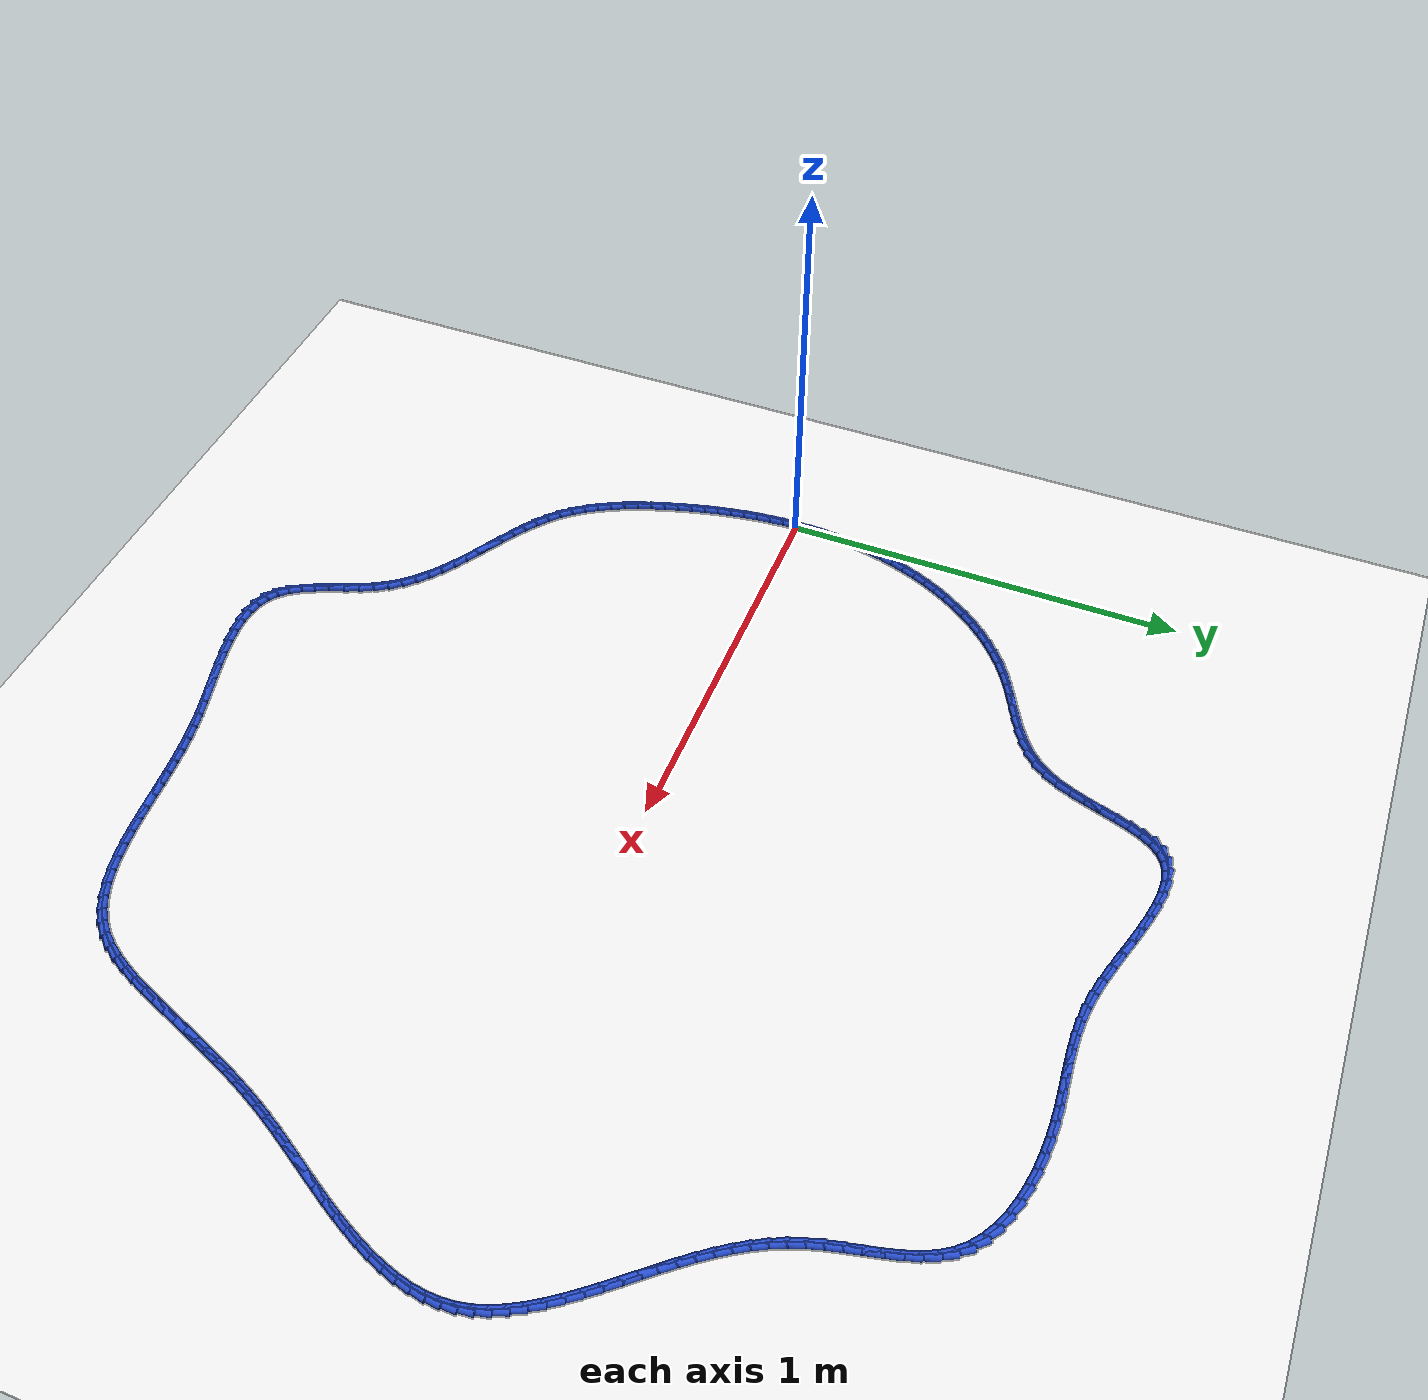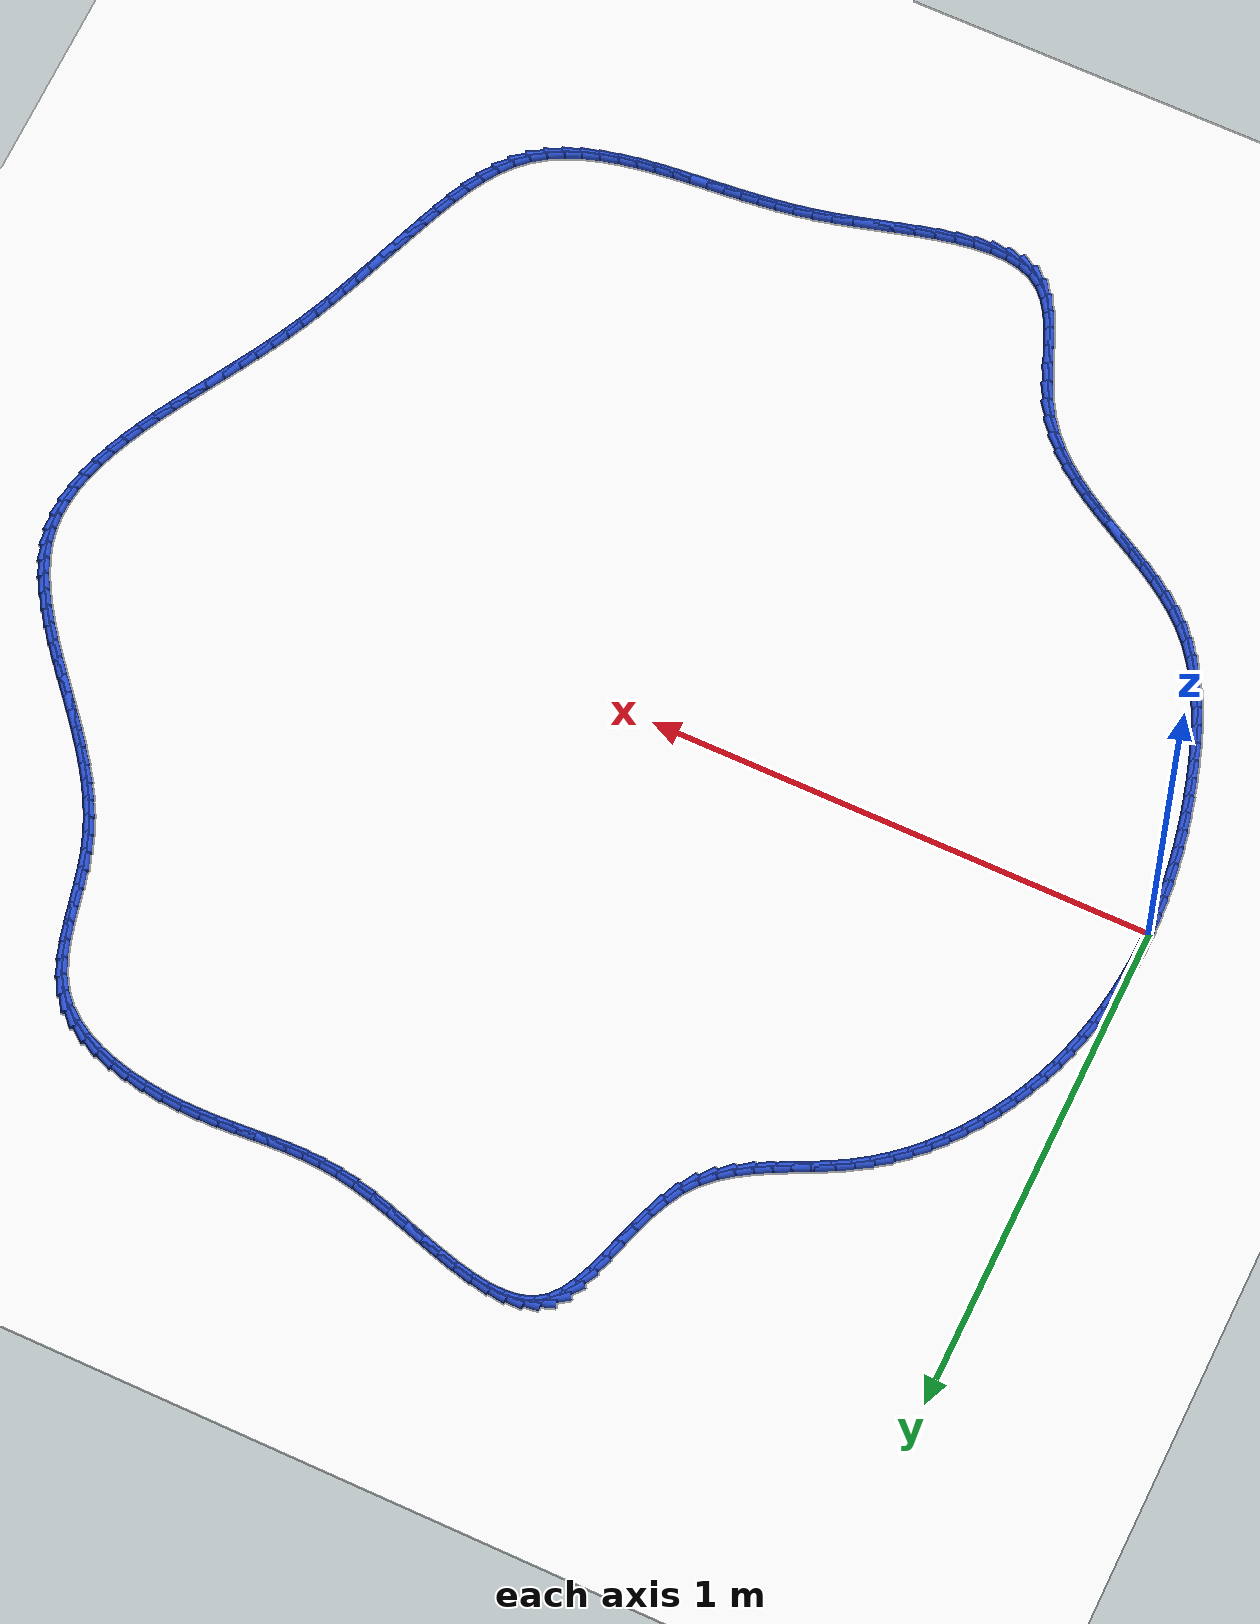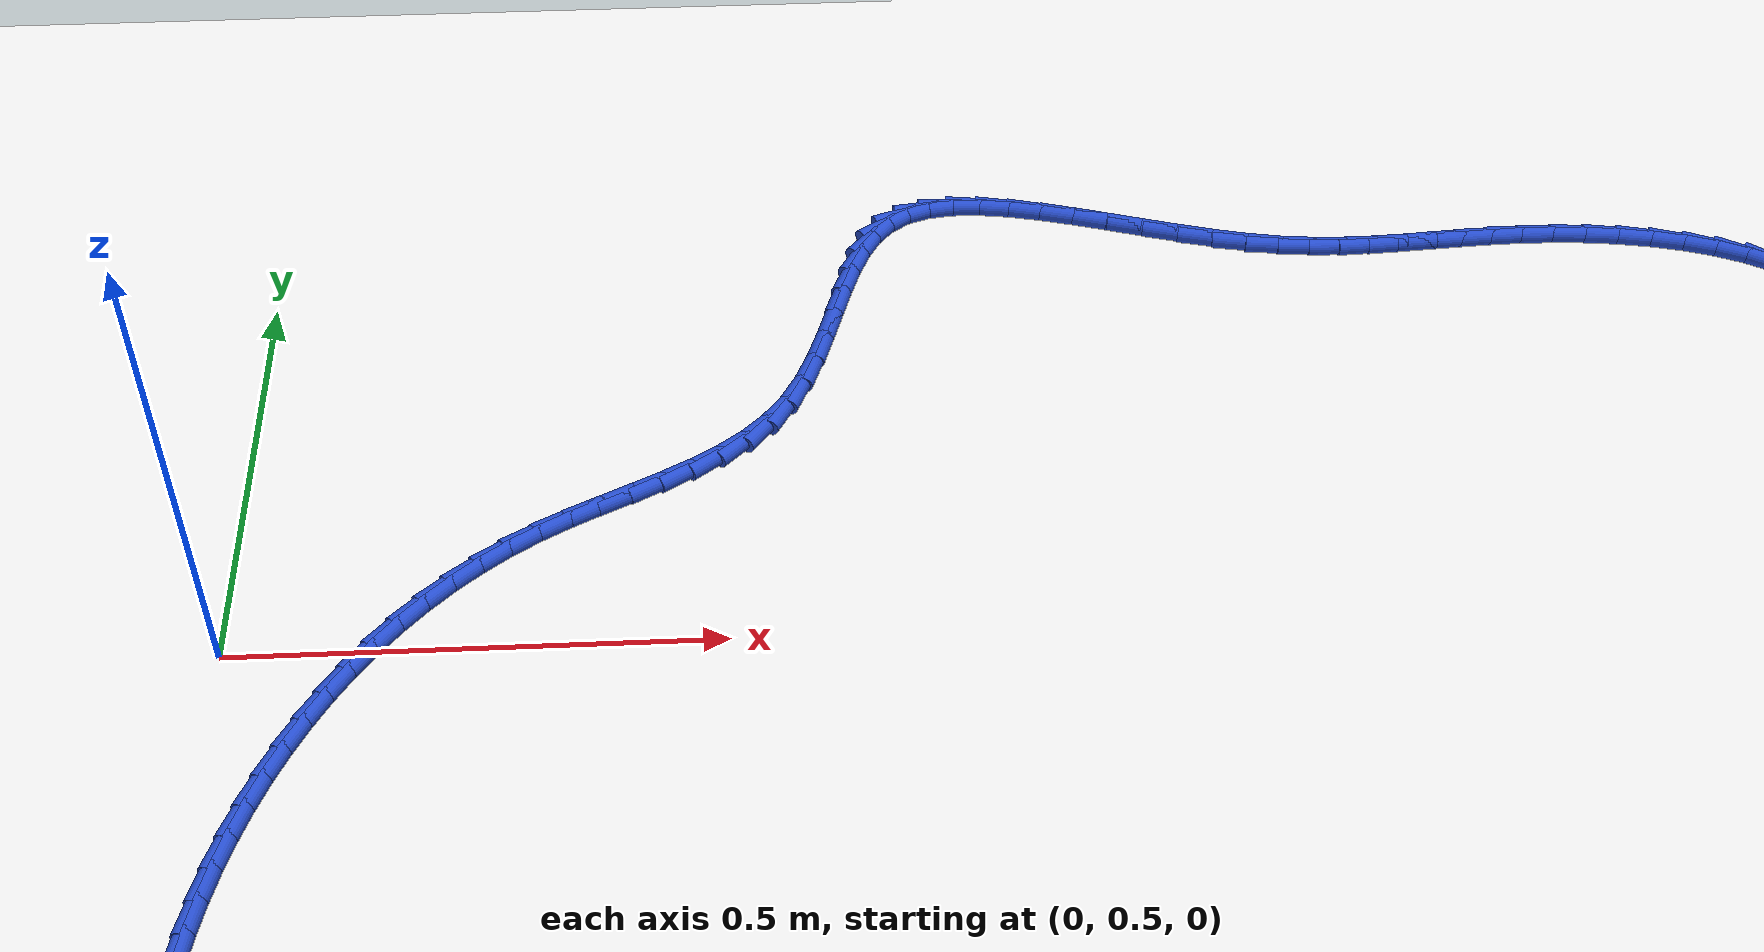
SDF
<sdf version="1.6">
 <world name="default">
  <light name="sun" type="directional">
   <pose>0 0 10 0 -0 0</pose>
   <diffuse>0.8 0.8 0.8 1</diffuse>
   <specular>0.2 0.2 0.2 1</specular>
   <attenuation>
    <range>1000</range>
    <constant>0.9</constant>
    <linear>0.01</linear>
    <quadratic>0.001</quadratic>
   </attenuation>
   <direction>-0.5 0.1 -0.9</direction>
  </light>
  <model name="ground_plane">
   <static>1</static>
   <link name="link">
    <collision name="collision">
     <geometry><plane><normal>0 0 1</normal><size>100 100</size></plane></geometry>
     <surface><friction><ode><mu>100</mu><mu2>50</mu2></ode></friction></surface>
    </collision>
    <visual name="visual">
     <cast_shadows>0</cast_shadows>
     <geometry><plane><normal>0 0 1</normal><size>100 100</size></plane></geometry>
     <material>
      <script><uri>file://media/materials/scripts/gazebo.material</uri><name>Gazebo/WhiteGlow</name></script>
     </material>
    </visual>
   </link>
  </model>
  <gravity>0 0 -9.8</gravity>
  <magnetic_field>6e-06 2.3e-05 -4.2e-05</magnetic_field>
  <atmosphere type="adiabatic"/>
  <physics name="default_physics" default="0" type="ode">
   <max_step_size>0.001</max_step_size>
   <real_time_factor>1</real_time_factor>
   <real_time_update_rate>1000</real_time_update_rate>
  </physics>
  <scene><ambient>0.4 0.4 0.4 1</ambient><background>0.7 0.7 0.7 1</background><shadows>1</shadows></scene>
  <spherical_coordinates>
   <surface_model>EARTH_WGS84</surface_model>
   <latitude_deg>0</latitude_deg>
   <longitude_deg>0</longitude_deg>
   <elevation>0</elevation>
   <heading_deg>0</heading_deg>
  </spherical_coordinates>
  <model name="line">
   <link name="link_0">
    <pose>-4.336808689942018e-18 -1.1796119636642288e-16 0.01 0 1.57 1.568800639922885</pose>
    <collision name="collision">
     <geometry><cylinder><radius>0.01</radius><length>0.08</length></cylinder></geometry>
    </collision>
    <visual name="visual">
     <material>
      <script><name>Gazebo/Blue</name><uri>file://media/materials/scripts/gazebo.material</uri></script>
     </material>
     <geometry><cylinder><radius>0.01</radius><length>0.08</length></cylinder></geometry>
    </visual>
   </link>
   <link name="link_1">
    <pose>6.942134410869392e-05 0.034785643438998634 0.01 0 1.57 1.5328198648100113</pose>
    <collision name="collision">
     <geometry><cylinder><radius>0.01</radius><length>0.08</length></cylinder></geometry>
    </collision>
    <visual name="visual">
     <material>
      <script><name>Gazebo/Blue</name><uri>file://media/materials/scripts/gazebo.material</uri></script>
     </material>
     <geometry><cylinder><radius>0.01</radius><length>0.08</length></cylinder></geometry>
    </visual>
   </link>
   <link name="link_2">
    <pose>0.0013932022842789277 0.06962681660383616 0.01 0 1.57 1.4957371810992248</pose>
    <collision name="collision">
     <geometry><cylinder><radius>0.01</radius><length>0.08</length></cylinder></geometry>
    </collision>
    <visual name="visual">
     <material>
      <script><name>Gazebo/Blue</name><uri>file://media/materials/scripts/gazebo.material</uri></script>
     </material>
     <geometry><cylinder><radius>0.01</radius><length>0.08</length></cylinder></geometry>
    </visual>
   </link>
   <link name="link_3">
    <pose>0.004012831644318548 0.10446211791155681 0.01 0 1.57 1.4574734331015686</pose>
    <collision name="collision">
     <geometry><cylinder><radius>0.01</radius><length>0.08</length></cylinder></geometry>
    </collision>
    <visual name="visual">
     <material>
      <script><name>Gazebo/Blue</name><uri>file://media/materials/scripts/gazebo.material</uri></script>
     </material>
     <geometry><cylinder><radius>0.01</radius><length>0.08</length></cylinder></geometry>
    </visual>
   </link>
   <link name="link_4">
    <pose>0.007969798248035407 0.13923014577920503 0.01 0 1.57 1.4179591411402652</pose>
    <collision name="collision">
     <geometry><cylinder><radius>0.01</radius><length>0.08</length></cylinder></geometry>
    </collision>
    <visual name="visual">
     <material>
      <script><name>Gazebo/Blue</name><uri>file://media/materials/scripts/gazebo.material</uri></script>
     </material>
     <geometry><cylinder><radius>0.01</radius><length>0.08</length></cylinder></geometry>
    </visual>
   </link>
   <link name="link_5">
    <pose>0.013305590919237355 0.17386949862382514 0.01 0 1.57 1.3771366664826474</pose>
    <collision name="collision">
     <geometry><cylinder><radius>0.01</radius><length>0.08</length></cylinder></geometry>
    </collision>
    <visual name="visual">
     <material>
      <script><name>Gazebo/Blue</name><uri>file://media/materials/scripts/gazebo.material</uri></script>
     </material>
     <geometry><cylinder><radius>0.01</radius><length>0.08</length></cylinder></geometry>
    </visual>
   </link>
   <link name="link_6">
    <pose>0.020061698481732258 0.20831877486246167 0.01 0 1.57 1.3349627168937246</pose>
    <collision name="collision">
     <geometry><cylinder><radius>0.01</radius><length>0.08</length></cylinder></geometry>
    </collision>
    <visual name="visual">
     <material>
      <script><name>Gazebo/Blue</name><uri>file://media/materials/scripts/gazebo.material</uri></script>
     </material>
     <geometry><cylinder><radius>0.01</radius><length>0.08</length></cylinder></geometry>
    </visual>
   </link>
   <link name="link_7">
    <pose>0.02827960975932797 0.24251657291215897 0.01 0 1.57 1.2914111258414969</pose>
    <collision name="collision">
     <geometry><cylinder><radius>0.01</radius><length>0.08</length></cylinder></geometry>
    </collision>
    <visual name="visual">
     <material>
      <script><name>Gazebo/Blue</name><uri>file://media/materials/scripts/gazebo.material</uri></script>
     </material>
     <geometry><cylinder><radius>0.01</radius><length>0.08</length></cylinder></geometry>
    </visual>
   </link>
   <link name="link_8">
    <pose>0.03800081357583232 0.27640149118996127 0.01 0 1.57 1.2464757983543455</pose>
    <collision name="collision">
     <geometry><cylinder><radius>0.01</radius><length>0.08</length></cylinder></geometry>
    </collision>
    <visual name="visual">
     <material>
      <script><name>Gazebo/Blue</name><uri>file://media/materials/scripts/gazebo.material</uri></script>
     </material>
     <geometry><cylinder><radius>0.01</radius><length>0.08</length></cylinder></geometry>
    </visual>
   </link>
   <link name="link_9">
    <pose>0.04926679858608168 0.30991212789948186 0.01 0 1.57 1.2002997846877717</pose>
    <collision name="collision">
     <geometry><cylinder><radius>0.01</radius><length>0.08</length></cylinder></geometry>
    </collision>
    <visual name="visual">
     <material>
      <script><name>Gazebo/Blue</name><uri>file://media/materials/scripts/gazebo.material</uri></script>
     </material>
     <geometry><cylinder><radius>0.01</radius><length>0.08</length></cylinder></geometry>
    </visual>
   </link>
   <link name="link_10">
    <pose>0.06210962696470761 0.3429751744702558 0.01 0 1.57 1.1532583030085948</pose>
    <collision name="collision">
     <geometry><cylinder><radius>0.01</radius><length>0.08</length></cylinder></geometry>
    </collision>
    <visual name="visual">
     <material>
      <script><name>Gazebo/Blue</name><uri>file://media/materials/scripts/gazebo.material</uri></script>
     </material>
     <geometry><cylinder><radius>0.01</radius><length>0.08</length></cylinder></geometry>
    </visual>
   </link>
   <link name="link_11">
    <pose>0.07652657323071264 0.37547338135413766 0.01 0 1.57 1.1052057215503837</pose>
    <collision name="collision">
     <geometry><cylinder><radius>0.01</radius><length>0.08</length></cylinder></geometry>
    </collision>
    <visual name="visual">
     <material>
      <script><name>Gazebo/Blue</name><uri>file://media/materials/scripts/gazebo.material</uri></script>
     </material>
     <geometry><cylinder><radius>0.01</radius><length>0.08</length></cylinder></geometry>
    </visual>
   </link>
   <link name="link_12">
    <pose>0.09250688889635973 0.407279364984069 0.01 0 1.57 1.0558829300887649</pose>
    <collision name="collision">
     <geometry><cylinder><radius>0.01</radius><length>0.08</length></cylinder></geometry>
    </collision>
    <visual name="visual">
     <material>
      <script><name>Gazebo/Blue</name><uri>file://media/materials/scripts/gazebo.material</uri></script>
     </material>
     <geometry><cylinder><radius>0.01</radius><length>0.08</length></cylinder></geometry>
    </visual>
   </link>
   <link name="link_13">
    <pose>0.11003982547391183 0.43826574179299205 0.01 0 1.57 1.0050430744310703</pose>
    <collision name="collision">
     <geometry><cylinder><radius>0.01</radius><length>0.08</length></cylinder></geometry>
    </collision>
    <visual name="visual">
     <material>
      <script><name>Gazebo/Blue</name><uri>file://media/materials/scripts/gazebo.material</uri></script>
     </material>
     <geometry><cylinder><radius>0.01</radius><length>0.08</length></cylinder></geometry>
    </visual>
   </link>
   <link name="link_14">
    <pose>0.12911463447563182 0.4683051282138483 0.01 0 1.57 0.9524551473889792</pose>
    <collision name="collision">
     <geometry><cylinder><radius>0.01</radius><length>0.08</length></cylinder></geometry>
    </collision>
    <visual name="visual">
     <material>
      <script><name>Gazebo/Blue</name><uri>file://media/materials/scripts/gazebo.material</uri></script>
     </material>
     <geometry><cylinder><radius>0.01</radius><length>0.08</length></cylinder></geometry>
    </visual>
   </link>
   <link name="link_15">
    <pose>0.1497205674137826 0.49727014067957964 0.01 0 1.57 0.8979094869843361</pose>
    <collision name="collision">
     <geometry><cylinder><radius>0.01</radius><length>0.08</length></cylinder></geometry>
    </collision>
    <visual name="visual">
     <material>
      <script><name>Gazebo/Blue</name><uri>file://media/materials/scripts/gazebo.material</uri></script>
     </material>
     <geometry><cylinder><radius>0.01</radius><length>0.08</length></cylinder></geometry>
    </visual>
   </link>
   <link name="link_16">
    <pose>0.1718468758006272 0.525033395623128 0.01 0 1.57 0.8412253683001695</pose>
    <collision name="collision">
     <geometry><cylinder><radius>0.01</radius><length>0.08</length></cylinder></geometry>
    </collision>
    <visual name="visual">
     <material>
      <script><name>Gazebo/Blue</name><uri>file://media/materials/scripts/gazebo.material</uri></script>
     </material>
     <geometry><cylinder><radius>0.01</radius><length>0.08</length></cylinder></geometry>
    </visual>
   </link>
   <link name="link_17">
    <pose>0.19548281114842855 0.5514675094774353 0.01 0 1.57 0.7822607343846165</pose>
    <collision name="collision">
     <geometry><cylinder><radius>0.01</radius><length>0.08</length></cylinder></geometry>
    </collision>
    <visual name="visual">
     <material>
      <script><name>Gazebo/Blue</name><uri>file://media/materials/scripts/gazebo.material</uri></script>
     </material>
     <geometry><cylinder><radius>0.01</radius><length>0.08</length></cylinder></geometry>
    </visual>
   </link>
   <link name="link_18">
    <pose>0.2206176249694495 0.5764450986754431 0.01 0 1.57 0.7209238612460389</pose>
    <collision name="collision">
     <geometry><cylinder><radius>0.01</radius><length>0.08</length></cylinder></geometry>
    </collision>
    <visual name="visual">
     <material>
      <script><name>Gazebo/Blue</name><uri>file://media/materials/scripts/gazebo.material</uri></script>
     </material>
     <geometry><cylinder><radius>0.01</radius><length>0.08</length></cylinder></geometry>
    </visual>
   </link>
   <link name="link_19">
    <pose>0.24724056877595305 0.5998387796500934 0.01 0 1.57 0.6571863731728453</pose>
    <collision name="collision">
     <geometry><cylinder><radius>0.01</radius><length>0.08</length></cylinder></geometry>
    </collision>
    <visual name="visual">
     <material>
      <script><name>Gazebo/Blue</name><uri>file://media/materials/scripts/gazebo.material</uri></script>
     </material>
     <geometry><cylinder><radius>0.01</radius><length>0.08</length></cylinder></geometry>
    </visual>
   </link>
   <link name="link_20">
    <pose>0.2753408940802021 0.6215211688343278 0.01 0 1.57 0.5910965270302646</pose>
    <collision name="collision">
     <geometry><cylinder><radius>0.01</radius><length>0.08</length></cylinder></geometry>
    </collision>
    <visual name="visual">
     <material>
      <script><name>Gazebo/Blue</name><uri>file://media/materials/scripts/gazebo.material</uri></script>
     </material>
     <geometry><cylinder><radius>0.01</radius><length>0.08</length></cylinder></geometry>
    </visual>
   </link>
   <link name="link_21">
    <pose>0.3049078523944595 0.6413648826610885 0.01 0 1.57 0.5262979814604454</pose>
    <collision name="collision">
     <geometry><cylinder><radius>0.01</radius><length>0.08</length></cylinder></geometry>
    </collision>
    <visual name="visual">
     <material>
      <script><name>Gazebo/Blue</name><uri>file://media/materials/scripts/gazebo.material</uri></script>
     </material>
     <geometry><cylinder><radius>0.01</radius><length>0.08</length></cylinder></geometry>
    </visual>
   </link>
   <link name="link_22">
    <pose>0.33585827709112476 0.6593456815773934 0.01 0 1.57 0.48171743994191635</pose>
    <collision name="collision">
     <geometry><cylinder><radius>0.01</radius><length>0.08</length></cylinder></geometry>
    </collision>
    <visual name="visual">
     <material>
      <script><name>Gazebo/Blue</name><uri>file://media/materials/scripts/gazebo.material</uri></script>
     </material>
     <geometry><cylinder><radius>0.01</radius><length>0.08</length></cylinder></geometry>
    </visual>
   </link>
   <link name="link_23">
    <pose>0.3677151314851315 0.676000308939072 0.01 0 1.57 0.4631127114034183</pose>
    <collision name="collision">
     <geometry><cylinder><radius>0.01</radius><length>0.08</length></cylinder></geometry>
    </collision>
    <visual name="visual">
     <material>
      <script><name>Gazebo/Blue</name><uri>file://media/materials/scripts/gazebo.material</uri></script>
     </material>
     <geometry><cylinder><radius>0.01</radius><length>0.08</length></cylinder></geometry>
    </visual>
   </link>
   <link name="link_24">
    <pose>0.39986811786411736 0.6920553096806908 0.01 0 1.57 0.4702268618535628</pose>
    <collision name="collision">
     <geometry><cylinder><radius>0.01</radius><length>0.08</length></cylinder></geometry>
    </collision>
    <visual name="visual">
     <material>
      <script><name>Gazebo/Blue</name><uri>file://media/materials/scripts/gazebo.material</uri></script>
     </material>
     <geometry><cylinder><radius>0.01</radius><length>0.08</length></cylinder></geometry>
    </visual>
   </link>
   <link name="link_25">
    <pose>0.4317068330319789 0.7082373789756444 0.01 0 1.57 0.5036651452503476</pose>
    <collision name="collision">
     <geometry><cylinder><radius>0.01</radius><length>0.08</length></cylinder></geometry>
    </collision>
    <visual name="visual">
     <material>
      <script><name>Gazebo/Blue</name><uri>file://media/materials/scripts/gazebo.material</uri></script>
     </material>
     <geometry><cylinder><radius>0.01</radius><length>0.08</length></cylinder></geometry>
    </visual>
   </link>
   <link name="link_26">
    <pose>0.46262087379261235 0.725273211997327 0.01 0 1.57 0.564802947789508</pose>
    <collision name="collision">
     <geometry><cylinder><radius>0.01</radius><length>0.08</length></cylinder></geometry>
    </collision>
    <visual name="visual">
     <material>
      <script><name>Gazebo/Blue</name><uri>file://media/materials/scripts/gazebo.material</uri></script>
     </material>
     <geometry><cylinder><radius>0.01</radius><length>0.08</length></cylinder></geometry>
    </visual>
   </link>
   <link name="link_27">
    <pose>0.49199983694991395 0.7438895039191332 0.01 0 1.57 0.6551097158264244</pose>
    <collision name="collision">
     <geometry><cylinder><radius>0.01</radius><length>0.08</length></cylinder></geometry>
    </collision>
    <visual name="visual">
     <material>
      <script><name>Gazebo/Blue</name><uri>file://media/materials/scripts/gazebo.material</uri></script>
     </material>
     <geometry><cylinder><radius>0.01</radius><length>0.08</length></cylinder></geometry>
    </visual>
   </link>
   <link name="link_28">
    <pose>0.5192333193077802 0.7648129499144577 0.01 0 1.57 0.7746562567084156</pose>
    <collision name="collision">
     <geometry><cylinder><radius>0.01</radius><length>0.08</length></cylinder></geometry>
    </collision>
    <visual name="visual">
     <material>
      <script><name>Gazebo/Blue</name><uri>file://media/materials/scripts/gazebo.material</uri></script>
     </material>
     <geometry><cylinder><radius>0.01</radius><length>0.08</length></cylinder></geometry>
    </visual>
   </link>
   <link name="link_29">
    <pose>0.5437109176701073 0.7887702451566949 0.01 0 1.57 0.9197677555701234</pose>
    <collision name="collision">
     <geometry><cylinder><radius>0.01</radius><length>0.08</length></cylinder></geometry>
    </collision>
    <visual name="visual">
     <material>
      <script><name>Gazebo/Blue</name><uri>file://media/materials/scripts/gazebo.material</uri></script>
     </material>
     <geometry><cylinder><radius>0.01</radius><length>0.08</length></cylinder></geometry>
    </visual>
   </link>
   <link name="link_30">
    <pose>0.5648246873275268 0.8164848359482298 0.01 0 1.57 1.0639257600568524</pose>
    <collision name="collision">
     <geometry><cylinder><radius>0.01</radius><length>0.08</length></cylinder></geometry>
    </collision>
    <visual name="visual">
     <material>
      <script><name>Gazebo/Blue</name><uri>file://media/materials/scripts/gazebo.material</uri></script>
     </material>
     <geometry><cylinder><radius>0.01</radius><length>0.08</length></cylinder></geometry>
    </visual>
   </link>
   <link name="link_31">
    <pose>0.5823904411315697 0.848120176286004 0.01 0 1.57 1.1674382508379675</pose>
    <collision name="collision">
     <geometry><cylinder><radius>0.01</radius><length>0.08</length></cylinder></geometry>
    </collision>
    <visual name="visual">
     <material>
      <script><name>Gazebo/Blue</name><uri>file://media/materials/scripts/gazebo.material</uri></script>
     </material>
     <geometry><cylinder><radius>0.01</radius><length>0.08</length></cylinder></geometry>
    </visual>
   </link>
   <link name="link_32">
    <pose>0.5971255657062029 0.8826482974716736 0.01 0 1.57 1.2328137088379727</pose>
    <collision name="collision">
     <geometry><cylinder><radius>0.01</radius><length>0.08</length></cylinder></geometry>
    </collision>
    <visual name="visual">
     <material>
      <script><name>Gazebo/Blue</name><uri>file://media/materials/scripts/gazebo.material</uri></script>
     </material>
     <geometry><cylinder><radius>0.01</radius><length>0.08</length></cylinder></geometry>
    </visual>
   </link>
   <link name="link_33">
    <pose>0.6098629126268238 0.918888644775836 0.01 0 1.57 1.2659018494557777</pose>
    <collision name="collision">
     <geometry><cylinder><radius>0.01</radius><length>0.08</length></cylinder></geometry>
    </collision>
    <visual name="visual">
     <material>
      <script><name>Gazebo/Blue</name><uri>file://media/materials/scripts/gazebo.material</uri></script>
     </material>
     <geometry><cylinder><radius>0.01</radius><length>0.08</length></cylinder></geometry>
    </visual>
   </link>
   <link name="link_34">
    <pose>0.6214353334688297 0.9556606634690878 0.01 0 1.57 1.2691258530796752</pose>
    <collision name="collision">
     <geometry><cylinder><radius>0.01</radius><length>0.08</length></cylinder></geometry>
    </collision>
    <visual name="visual">
     <material>
      <script><name>Gazebo/Blue</name><uri>file://media/materials/scripts/gazebo.material</uri></script>
     </material>
     <geometry><cylinder><radius>0.01</radius><length>0.08</length></cylinder></geometry>
    </visual>
   </link>
   <link name="link_35">
    <pose>0.6326756798076177 0.9917837988220257 0.01 0 1.57 1.2409351931149395</pose>
    <collision name="collision">
     <geometry><cylinder><radius>0.01</radius><length>0.08</length></cylinder></geometry>
    </collision>
    <visual name="visual">
     <material>
      <script><name>Gazebo/Blue</name><uri>file://media/materials/scripts/gazebo.material</uri></script>
     </material>
     <geometry><cylinder><radius>0.01</radius><length>0.08</length></cylinder></geometry>
    </visual>
   </link>
   <link name="link_36">
    <pose>0.6444168032185855 1.0260774961052466 0.01 0 1.57 1.1749196223753062</pose>
    <collision name="collision">
     <geometry><cylinder><radius>0.01</radius><length>0.08</length></cylinder></geometry>
    </collision>
    <visual name="visual">
     <material>
      <script><name>Gazebo/Blue</name><uri>file://media/materials/scripts/gazebo.material</uri></script>
     </material>
     <geometry><cylinder><radius>0.01</radius><length>0.08</length></cylinder></geometry>
    </visual>
   </link>
   <link name="link_37">
    <pose>0.6574915552771301 1.057361200589347 0.01 0 1.57 1.058369534545176</pose>
    <collision name="collision">
     <geometry><cylinder><radius>0.01</radius><length>0.08</length></cylinder></geometry>
    </collision>
    <visual name="visual">
     <material>
      <script><name>Gazebo/Blue</name><uri>file://media/materials/scripts/gazebo.material</uri></script>
     </material>
     <geometry><cylinder><radius>0.01</radius><length>0.08</length></cylinder></geometry>
    </visual>
   </link>
   <link name="link_38">
    <pose>0.6727327875586487 1.0844543575449235 0.01 0 1.57 0.8722974416425814</pose>
    <collision name="collision">
     <geometry><cylinder><radius>0.01</radius><length>0.08</length></cylinder></geometry>
    </collision>
    <visual name="visual">
     <material>
      <script><name>Gazebo/Blue</name><uri>file://media/materials/scripts/gazebo.material</uri></script>
     </material>
     <geometry><cylinder><radius>0.01</radius><length>0.08</length></cylinder></geometry>
    </visual>
   </link>
   <link name="link_39">
    <pose>0.690973351638539 1.1061764122425735 0.01 0 1.57 0.6093214626110365</pose>
    <collision name="collision">
     <geometry><cylinder><radius>0.01</radius><length>0.08</length></cylinder></geometry>
    </collision>
    <visual name="visual">
     <material>
      <script><name>Gazebo/Blue</name><uri>file://media/materials/scripts/gazebo.material</uri></script>
     </material>
     <geometry><cylinder><radius>0.01</radius><length>0.08</length></cylinder></geometry>
    </visual>
   </link>
   <link name="link_40">
    <pose>0.712942071337157 1.12150858704878 0.01 0 1.57 0.3432235566435931</pose>
    <collision name="collision">
     <geometry><cylinder><radius>0.01</radius><length>0.08</length></cylinder></geometry>
    </collision>
    <visual name="visual">
     <material>
      <script><name>Gazebo/Blue</name><uri>file://media/materials/scripts/gazebo.material</uri></script>
     </material>
     <geometry><cylinder><radius>0.01</radius><length>0.08</length></cylinder></geometry>
    </visual>
   </link>
   <link name="link_41">
    <pose>0.7385729055669421 1.130668225751413 0.01 0 1.57 0.130055325957764</pose>
    <collision name="collision">
     <geometry><cylinder><radius>0.01</radius><length>0.08</length></cylinder></geometry>
    </collision>
    <visual name="visual">
     <material>
      <script><name>Gazebo/Blue</name><uri>file://media/materials/scripts/gazebo.material</uri></script>
     </material>
     <geometry><cylinder><radius>0.01</radius><length>0.08</length></cylinder></geometry>
    </visual>
   </link>
   <link name="link_42">
    <pose>0.7674331036576405 1.1344429546682164 0.01 0 1.57 -0.02588274738965222</pose>
    <collision name="collision">
     <geometry><cylinder><radius>0.01</radius><length>0.08</length></cylinder></geometry>
    </collision>
    <visual name="visual">
     <material>
      <script><name>Gazebo/Blue</name><uri>file://media/materials/scripts/gazebo.material</uri></script>
     </material>
     <geometry><cylinder><radius>0.01</radius><length>0.08</length></cylinder></geometry>
    </visual>
   </link>
   <link name="link_43">
    <pose>0.7990879490780592 1.1336234572940662 0.01 0 1.57 -0.13508498575308453</pose>
    <collision name="collision">
     <geometry><cylinder><radius>0.01</radius><length>0.08</length></cylinder></geometry>
    </collision>
    <visual name="visual">
     <material>
      <script><name>Gazebo/Blue</name><uri>file://media/materials/scripts/gazebo.material</uri></script>
     </material>
     <geometry><cylinder><radius>0.01</radius><length>0.08</length></cylinder></geometry>
    </visual>
   </link>
   <link name="link_44">
    <pose>0.8331027252970042 1.1290004171238368 0.01 0 1.57 -0.20934949271723952</pose>
    <collision name="collision">
     <geometry><cylinder><radius>0.01</radius><length>0.08</length></cylinder></geometry>
    </collision>
    <visual name="visual">
     <material>
      <script><name>Gazebo/Blue</name><uri>file://media/materials/scripts/gazebo.material</uri></script>
     </material>
     <geometry><cylinder><radius>0.01</radius><length>0.08</length></cylinder></geometry>
    </visual>
   </link>
   <link name="link_45">
    <pose>0.8690427157832831 1.121364517652404 0.01 0 1.57 -0.25752226222784425</pose>
    <collision name="collision">
     <geometry><cylinder><radius>0.01</radius><length>0.08</length></cylinder></geometry>
    </collision>
    <visual name="visual">
     <material>
      <script><name>Gazebo/Blue</name><uri>file://media/materials/scripts/gazebo.material</uri></script>
     </material>
     <geometry><cylinder><radius>0.01</radius><length>0.08</length></cylinder></geometry>
    </visual>
   </link>
   <link name="link_46">
    <pose>0.9064732040057021 1.1115064423746435 0.01 0 1.57 -0.2853356858239661</pose>
    <collision name="collision">
     <geometry><cylinder><radius>0.01</radius><length>0.08</length></cylinder></geometry>
    </collision>
    <visual name="visual">
     <material>
      <script><name>Gazebo/Blue</name><uri>file://media/materials/scripts/gazebo.material</uri></script>
     </material>
     <geometry><cylinder><radius>0.01</radius><length>0.08</length></cylinder></geometry>
    </visual>
   </link>
   <link name="link_47">
    <pose>0.9449594734330677 1.1002168747854297 0.01 0 1.57 -0.2960993629154483</pose>
    <collision name="collision">
     <geometry><cylinder><radius>0.01</radius><length>0.08</length></cylinder></geometry>
    </collision>
    <visual name="visual">
     <material>
      <script><name>Gazebo/Blue</name><uri>file://media/materials/scripts/gazebo.material</uri></script>
     </material>
     <geometry><cylinder><radius>0.01</radius><length>0.08</length></cylinder></geometry>
    </visual>
   </link>
   <link name="link_48">
    <pose>0.9840668075341867 1.0882864983796383 0.01 0 1.57 -0.29127927100680845</pose>
    <collision name="collision">
     <geometry><cylinder><radius>0.01</radius><length>0.08</length></cylinder></geometry>
    </collision>
    <visual name="visual">
     <material>
      <script><name>Gazebo/Blue</name><uri>file://media/materials/scripts/gazebo.material</uri></script>
     </material>
     <geometry><cylinder><radius>0.01</radius><length>0.08</length></cylinder></geometry>
    </visual>
   </link>
   <link name="link_49">
    <pose>1.023360489777866 1.0765059966521442 0.01 0 1.57 -0.27080473262009763</pose>
    <collision name="collision">
     <geometry><cylinder><radius>0.01</radius><length>0.08</length></cylinder></geometry>
    </collision>
    <visual name="visual">
     <material>
      <script><name>Gazebo/Blue</name><uri>file://media/materials/scripts/gazebo.material</uri></script>
     </material>
     <geometry><cylinder><radius>0.01</radius><length>0.08</length></cylinder></geometry>
    </visual>
   </link>
   <link name="link_50">
    <pose>1.062405803632912 1.0656660530978226 0.01 0 1.57 -0.23312236808661627</pose>
    <collision name="collision">
     <geometry><cylinder><radius>0.01</radius><length>0.08</length></cylinder></geometry>
    </collision>
    <visual name="visual">
     <material>
      <script><name>Gazebo/Blue</name><uri>file://media/materials/scripts/gazebo.material</uri></script>
     </material>
     <geometry><cylinder><radius>0.01</radius><length>0.08</length></cylinder></geometry>
    </visual>
   </link>
   <link name="link_51">
    <pose>1.1007680325681322 1.0565573512115496 0.01 0 1.57 -0.1752799219053801</pose>
    <collision name="collision">
     <geometry><cylinder><radius>0.01</radius><length>0.08</length></cylinder></geometry>
    </collision>
    <visual name="visual">
     <material>
      <script><name>Gazebo/Blue</name><uri>file://media/materials/scripts/gazebo.material</uri></script>
     </material>
     <geometry><cylinder><radius>0.01</radius><length>0.08</length></cylinder></geometry>
    </visual>
   </link>
   <link name="link_52">
    <pose>1.1380181311865412 1.0499604591706917 0.01 0 1.57 -0.10566344640412224</pose>
    <collision name="collision">
     <geometry><cylinder><radius>0.01</radius><length>0.08</length></cylinder></geometry>
    </collision>
    <visual name="visual">
     <material>
      <script><name>Gazebo/Blue</name><uri>file://media/materials/scripts/gazebo.material</uri></script>
     </material>
     <geometry><cylinder><radius>0.01</radius><length>0.08</length></cylinder></geometry>
    </visual>
   </link>
   <link name="link_53">
    <pose>1.174014799291494 1.0461427084780193 0.01 0 1.57 -0.04329514868922163</pose>
    <collision name="collision">
     <geometry><cylinder><radius>0.01</radius><length>0.08</length></cylinder></geometry>
    </collision>
    <visual name="visual">
     <material>
      <script><name>Gazebo/Blue</name><uri>file://media/materials/scripts/gazebo.material</uri></script>
     </material>
     <geometry><cylinder><radius>0.01</radius><length>0.08</length></cylinder></geometry>
    </visual>
   </link>
   <link name="link_54">
    <pose>1.2090349079151483 1.0446255595995952 0.01 0 1.57 0.007167260759064347</pose>
    <collision name="collision">
     <geometry><cylinder><radius>0.01</radius><length>0.08</length></cylinder></geometry>
    </collision>
    <visual name="visual">
     <material>
      <script><name>Gazebo/Blue</name><uri>file://media/materials/scripts/gazebo.material</uri></script>
     </material>
     <geometry><cylinder><radius>0.01</radius><length>0.08</length></cylinder></geometry>
    </visual>
   </link>
   <link name="link_55">
    <pose>1.2433882325027603 1.0448717830510055 0.01 0 1.57 0.04328253535785284</pose>
    <collision name="collision">
     <geometry><cylinder><radius>0.01</radius><length>0.08</length></cylinder></geometry>
    </collision>
    <visual name="visual">
     <material>
      <script><name>Gazebo/Blue</name><uri>file://media/materials/scripts/gazebo.material</uri></script>
     </material>
     <geometry><cylinder><radius>0.01</radius><length>0.08</length></cylinder></geometry>
    </visual>
   </link>
   <link name="link_56">
    <pose>1.2773845484995852 1.0463441493478358 0.01 0 1.57 0.06357658999469958</pose>
    <collision name="collision">
     <geometry><cylinder><radius>0.01</radius><length>0.08</length></cylinder></geometry>
    </collision>
    <visual name="visual">
     <material>
      <script><name>Gazebo/Blue</name><uri>file://media/materials/scripts/gazebo.material</uri></script>
     </material>
     <geometry><cylinder><radius>0.01</radius><length>0.08</length></cylinder></geometry>
    </visual>
   </link>
   <link name="link_57">
    <pose>1.3113336313508788 1.0485054290056723 0.01 0 1.57 0.06750480699866826</pose>
    <collision name="collision">
     <geometry><cylinder><radius>0.01</radius><length>0.08</length></cylinder></geometry>
    </collision>
    <visual name="visual">
     <material>
      <script><name>Gazebo/Blue</name><uri>file://media/materials/scripts/gazebo.material</uri></script>
     </material>
     <geometry><cylinder><radius>0.01</radius><length>0.08</length></cylinder></geometry>
    </visual>
   </link>
   <link name="link_58">
    <pose>1.3455452565018966 1.0508183925401013 0.01 0 1.57 0.05535453281046241</pose>
    <collision name="collision">
     <geometry><cylinder><radius>0.01</radius><length>0.08</length></cylinder></geometry>
    </collision>
    <visual name="visual">
     <material>
      <script><name>Gazebo/Blue</name><uri>file://media/materials/scripts/gazebo.material</uri></script>
     </material>
     <geometry><cylinder><radius>0.01</radius><length>0.08</length></cylinder></geometry>
    </visual>
   </link>
   <link name="link_59">
    <pose>1.3803291993978948 1.0527458104667082 0.01 0 1.57 0.028160607774629663</pose>
    <collision name="collision">
     <geometry><cylinder><radius>0.01</radius><length>0.08</length></cylinder></geometry>
    </collision>
    <visual name="visual">
     <material>
      <script><name>Gazebo/Blue</name><uri>file://media/materials/scripts/gazebo.material</uri></script>
     </material>
     <geometry><cylinder><radius>0.01</radius><length>0.08</length></cylinder></geometry>
    </visual>
   </link>
   <link name="link_60">
    <pose>1.4159952354841294 1.0537504533010795 0.01 0 1.57 -0.011588158921155601</pose>
    <collision name="collision">
     <geometry><cylinder><radius>0.01</radius><length>0.08</length></cylinder></geometry>
    </collision>
    <visual name="visual">
     <material>
      <script><name>Gazebo/Blue</name><uri>file://media/materials/scripts/gazebo.material</uri></script>
     </material>
     <geometry><cylinder><radius>0.01</radius><length>0.08</length></cylinder></geometry>
    </visual>
   </link>
   <link name="link_61">
    <pose>1.452768156756894 1.0533243037699809 0.01 0 1.57 -0.05762361508047386</pose>
    <collision name="collision">
     <geometry><cylinder><radius>0.01</radius><length>0.08</length></cylinder></geometry>
    </collision>
    <visual name="visual">
     <material>
      <script><name>Gazebo/Blue</name><uri>file://media/materials/scripts/gazebo.material</uri></script>
     </material>
     <geometry><cylinder><radius>0.01</radius><length>0.08</length></cylinder></geometry>
    </visual>
   </link>
   <link name="link_62">
    <pose>1.4902896422493075 1.051159783853118 0.01 0 1.57 -0.1091128675000452</pose>
    <collision name="collision">
     <geometry><cylinder><radius>0.01</radius><length>0.08</length></cylinder></geometry>
    </collision>
    <visual name="visual">
     <material>
      <script><name>Gazebo/Blue</name><uri>file://media/materials/scripts/gazebo.material</uri></script>
     </material>
     <geometry><cylinder><radius>0.01</radius><length>0.08</length></cylinder></geometry>
    </visual>
   </link>
   <link name="link_63">
    <pose>1.5279566323581455 1.0470334419903047 0.01 0 1.57 -0.168020931062326</pose>
    <collision name="collision">
     <geometry><cylinder><radius>0.01</radius><length>0.08</length></cylinder></geometry>
    </collision>
    <visual name="visual">
     <material>
      <script><name>Gazebo/Blue</name><uri>file://media/materials/scripts/gazebo.material</uri></script>
     </material>
     <geometry><cylinder><radius>0.01</radius><length>0.08</length></cylinder></geometry>
    </visual>
   </link>
   <link name="link_64">
    <pose>1.56516522751896 1.0407221153496284 0.01 0 1.57 -0.23670510793564642</pose>
    <collision name="collision">
     <geometry><cylinder><radius>0.01</radius><length>0.08</length></cylinder></geometry>
    </collision>
    <visual name="visual">
     <material>
      <script><name>Gazebo/Blue</name><uri>file://media/materials/scripts/gazebo.material</uri></script>
     </material>
     <geometry><cylinder><radius>0.01</radius><length>0.08</length></cylinder></geometry>
    </visual>
   </link>
   <link name="link_65">
    <pose>1.601311528167304 1.0320026410991774 0.01 0 1.57 -0.3180242158675875</pose>
    <collision name="collision">
     <geometry><cylinder><radius>0.01</radius><length>0.08</length></cylinder></geometry>
    </collision>
    <visual name="visual">
     <material>
      <script><name>Gazebo/Blue</name><uri>file://media/materials/scripts/gazebo.material</uri></script>
     </material>
     <geometry><cylinder><radius>0.01</radius><length>0.08</length></cylinder></geometry>
    </visual>
   </link>
   <link name="link_66">
    <pose>1.6357916347387291 1.0206518564070393 0.01 0 1.57 -0.41536106048401433</pose>
    <collision name="collision">
     <geometry><cylinder><radius>0.01</radius><length>0.08</length></cylinder></geometry>
    </collision>
    <visual name="visual">
     <material>
      <script><name>Gazebo/Blue</name><uri>file://media/materials/scripts/gazebo.material</uri></script>
     </material>
     <geometry><cylinder><radius>0.01</radius><length>0.08</length></cylinder></geometry>
    </visual>
   </link>
   <link name="link_67">
    <pose>1.6680016476687893 1.0064465984413022 0.01 0 1.57 -0.5323926812634643</pose>
    <collision name="collision">
     <geometry><cylinder><radius>0.01</radius><length>0.08</length></cylinder></geometry>
    </collision>
    <visual name="visual">
     <material>
      <script><name>Gazebo/Blue</name><uri>file://media/materials/scripts/gazebo.material</uri></script>
     </material>
     <geometry><cylinder><radius>0.01</radius><length>0.08</length></cylinder></geometry>
    </visual>
   </link>
   <link name="link_68">
    <pose>1.6973376673930352 0.9891637043700539 0.01 0 1.57 -0.6723119249832672</pose>
    <collision name="collision">
     <geometry><cylinder><radius>0.01</radius><length>0.08</length></cylinder></geometry>
    </collision>
    <visual name="visual">
     <material>
      <script><name>Gazebo/Blue</name><uri>file://media/materials/scripts/gazebo.material</uri></script>
     </material>
     <geometry><cylinder><radius>0.01</radius><length>0.08</length></cylinder></geometry>
    </visual>
   </link>
   <link name="link_69">
    <pose>1.7231957943470202 0.9685800113613825 0.01 0 1.57 -0.8360339346330957</pose>
    <collision name="collision">
     <geometry><cylinder><radius>0.01</radius><length>0.08</length></cylinder></geometry>
    </collision>
    <visual name="visual">
     <material>
      <script><name>Gazebo/Blue</name><uri>file://media/materials/scripts/gazebo.material</uri></script>
     </material>
     <geometry><cylinder><radius>0.01</radius><length>0.08</length></cylinder></geometry>
    </visual>
   </link>
   <link name="link_70">
    <pose>1.7449757973966125 0.9444745759520853 0.01 0 1.57 -1.0040285504825182</pose>
    <collision name="collision">
     <geometry><cylinder><radius>0.01</radius><length>0.08</length></cylinder></geometry>
    </collision>
    <visual name="visual">
     <material>
      <script><name>Gazebo/Blue</name><uri>file://media/materials/scripts/gazebo.material</uri></script>
     </material>
     <geometry><cylinder><radius>0.01</radius><length>0.08</length></cylinder></geometry>
    </visual>
   </link>
   <link name="link_71">
    <pose>1.762526095322999 0.9168978840091779 0.01 0 1.57 -1.138918047160862</pose>
    <collision name="collision">
     <geometry><cylinder><radius>0.01</radius><length>0.08</length></cylinder></geometry>
    </collision>
    <visual name="visual">
     <material>
      <script><name>Gazebo/Blue</name><uri>file://media/materials/scripts/gazebo.material</uri></script>
     </material>
     <geometry><cylinder><radius>0.01</radius><length>0.08</length></cylinder></geometry>
    </visual>
   </link>
   <link name="link_72">
    <pose>1.7765690291069722 0.886429136794912 0.01 0 1.57 -1.2366706399649796</pose>
    <collision name="collision">
     <geometry><cylinder><radius>0.01</radius><length>0.08</length></cylinder></geometry>
    </collision>
    <visual name="visual">
     <material>
      <script><name>Gazebo/Blue</name><uri>file://media/materials/scripts/gazebo.material</uri></script>
     </material>
     <geometry><cylinder><radius>0.01</radius><length>0.08</length></cylinder></geometry>
    </visual>
   </link>
   <link name="link_73">
    <pose>1.7879277084468503 0.8537084997767511 0.01 0 1.57 -1.3009106567137878</pose>
    <collision name="collision">
     <geometry><cylinder><radius>0.01</radius><length>0.08</length></cylinder></geometry>
    </collision>
    <visual name="visual">
     <material>
      <script><name>Gazebo/Blue</name><uri>file://media/materials/scripts/gazebo.material</uri></script>
     </material>
     <geometry><cylinder><radius>0.01</radius><length>0.08</length></cylinder></geometry>
    </visual>
   </link>
   <link name="link_74">
    <pose>1.797425243040953 0.8193761384221585 0.01 0 1.57 -1.3356113727087884</pose>
    <collision name="collision">
     <geometry><cylinder><radius>0.01</radius><length>0.08</length></cylinder></geometry>
    </collision>
    <visual name="visual">
     <material>
      <script><name>Gazebo/Blue</name><uri>file://media/materials/scripts/gazebo.material</uri></script>
     </material>
     <geometry><cylinder><radius>0.01</radius><length>0.08</length></cylinder></geometry>
    </visual>
   </link>
   <link name="link_75">
    <pose>1.8058847425875983 0.7840722181985972 0.01 0 1.57 -1.3434369711599339</pose>
    <collision name="collision">
     <geometry><cylinder><radius>0.01</radius><length>0.08</length></cylinder></geometry>
    </collision>
    <visual name="visual">
     <material>
      <script><name>Gazebo/Blue</name><uri>file://media/materials/scripts/gazebo.material</uri></script>
     </material>
     <geometry><cylinder><radius>0.01</radius><length>0.08</length></cylinder></geometry>
    </visual>
   </link>
   <link name="link_76">
    <pose>1.8141293167851058 0.7484369045735306 0.01 0 1.57 -1.325254975710259</pose>
    <collision name="collision">
     <geometry><cylinder><radius>0.01</radius><length>0.08</length></cylinder></geometry>
    </collision>
    <visual name="visual">
     <material>
      <script><name>Gazebo/Blue</name><uri>file://media/materials/scripts/gazebo.material</uri></script>
     </material>
     <geometry><cylinder><radius>0.01</radius><length>0.08</length></cylinder></geometry>
    </visual>
   </link>
   <link name="link_77">
    <pose>1.8229820753317942 0.7131103630144219 0.01 0 1.57 -1.2801198203482085</pose>
    <collision name="collision">
     <geometry><cylinder><radius>0.01</radius><length>0.08</length></cylinder></geometry>
    </collision>
    <visual name="visual">
     <material>
      <script><name>Gazebo/Blue</name><uri>file://media/materials/scripts/gazebo.material</uri></script>
     </material>
     <geometry><cylinder><radius>0.01</radius><length>0.08</length></cylinder></geometry>
    </visual>
   </link>
   <link name="link_78">
    <pose>1.8332661254076776 0.6787327567715427 0.01 0 1.57 -1.2118092849769024</pose>
    <collision name="collision">
     <geometry><cylinder><radius>0.01</radius><length>0.08</length></cylinder></geometry>
    </collision>
    <visual name="visual">
     <material>
      <script><name>Gazebo/Blue</name><uri>file://media/materials/scripts/gazebo.material</uri></script>
     </material>
     <geometry><cylinder><radius>0.01</radius><length>0.08</length></cylinder></geometry>
    </visual>
   </link>
   <link name="link_79">
    <pose>1.8456281841020479 0.6457889499911988 0.01 0 1.57 -1.1424005778273618</pose>
    <collision name="collision">
     <geometry><cylinder><radius>0.01</radius><length>0.08</length></cylinder></geometry>
    </collision>
    <visual name="visual">
     <material>
      <script><name>Gazebo/Blue</name><uri>file://media/materials/scripts/gazebo.material</uri></script>
     </material>
     <geometry><cylinder><radius>0.01</radius><length>0.08</length></cylinder></geometry>
    </visual>
   </link>
   <link name="link_80">
    <pose>1.860060083535181 0.6141872265340683 0.01 0 1.57 -1.0787247031281886</pose>
    <collision name="collision">
     <geometry><cylinder><radius>0.01</radius><length>0.08</length></cylinder></geometry>
    </collision>
    <visual name="visual">
     <material>
      <script><name>Gazebo/Blue</name><uri>file://media/materials/scripts/gazebo.material</uri></script>
     </material>
     <geometry><cylinder><radius>0.01</radius><length>0.08</length></cylinder></geometry>
    </visual>
   </link>
   <link name="link_81">
    <pose>1.8764017056601403 0.5837020887954455 0.01 0 1.57 -1.0220999563051238</pose>
    <collision name="collision">
     <geometry><cylinder><radius>0.01</radius><length>0.08</length></cylinder></geometry>
    </collision>
    <visual name="visual">
     <material>
      <script><name>Gazebo/Blue</name><uri>file://media/materials/scripts/gazebo.material</uri></script>
     </material>
     <geometry><cylinder><radius>0.01</radius><length>0.08</length></cylinder></geometry>
    </visual>
   </link>
   <link name="link_82">
    <pose>1.8944929324299862 0.5541080391706249 0.01 0 1.57 -0.9733984238061587</pose>
    <collision name="collision">
     <geometry><cylinder><radius>0.01</radius><length>0.08</length></cylinder></geometry>
    </collision>
    <visual name="visual">
     <material>
      <script><name>Gazebo/Blue</name><uri>file://media/materials/scripts/gazebo.material</uri></script>
     </material>
     <geometry><cylinder><radius>0.01</radius><length>0.08</length></cylinder></geometry>
    </visual>
   </link>
   <link name="link_83">
    <pose>1.914173645797782 0.5251795800549012 0.01 0 1.57 -0.9330755547395273</pose>
    <collision name="collision">
     <geometry><cylinder><radius>0.01</radius><length>0.08</length></cylinder></geometry>
    </collision>
    <visual name="visual">
     <material>
      <script><name>Gazebo/Blue</name><uri>file://media/materials/scripts/gazebo.material</uri></script>
     </material>
     <geometry><cylinder><radius>0.01</radius><length>0.08</length></cylinder></geometry>
    </visual>
   </link>
   <link name="link_84">
    <pose>1.9352837277165895 0.49669121384356907 0.01 0 1.57 -0.9012541939319493</pose>
    <collision name="collision">
     <geometry><cylinder><radius>0.01</radius><length>0.08</length></cylinder></geometry>
    </collision>
    <visual name="visual">
     <material>
      <script><name>Gazebo/Blue</name><uri>file://media/materials/scripts/gazebo.material</uri></script>
     </material>
     <geometry><cylinder><radius>0.01</radius><length>0.08</length></cylinder></geometry>
    </visual>
   </link>
   <link name="link_85">
    <pose>1.9576622187465444 0.46841802217715234 0.01 0 1.57 -0.8785754589700037</pose>
    <collision name="collision">
     <geometry><cylinder><radius>0.01</radius><length>0.08</length></cylinder></geometry>
    </collision>
    <visual name="visual">
     <material>
      <script><name>Gazebo/Blue</name><uri>file://media/materials/scripts/gazebo.material</uri></script>
     </material>
     <geometry><cylinder><radius>0.01</radius><length>0.08</length></cylinder></geometry>
    </visual>
   </link>
   <link name="link_86">
    <pose>1.9810614481243038 0.4401947818977395 0.01 0 1.57 -0.8659354689195341</pose>
    <collision name="collision">
     <geometry><cylinder><radius>0.01</radius><length>0.08</length></cylinder></geometry>
    </collision>
    <visual name="visual">
     <material>
      <script><name>Gazebo/Blue</name><uri>file://media/materials/scripts/gazebo.material</uri></script>
     </material>
     <geometry><cylinder><radius>0.01</radius><length>0.08</length></cylinder></geometry>
    </visual>
   </link>
   <link name="link_87">
    <pose>2.005072903560713 0.411966998953131 0.01 0 1.57 -0.8629419647385037</pose>
    <collision name="collision">
     <geometry><cylinder><radius>0.01</radius><length>0.08</length></cylinder></geometry>
    </collision>
    <visual name="visual">
     <material>
      <script><name>Gazebo/Blue</name><uri>file://media/materials/scripts/gazebo.material</uri></script>
     </material>
     <geometry><cylinder><radius>0.01</radius><length>0.08</length></cylinder></geometry>
    </visual>
   </link>
   <link name="link_88">
    <pose>2.0292706068475006 0.383692203459604 0.01 0 1.57 -0.8694146638724691</pose>
    <collision name="collision">
     <geometry><cylinder><radius>0.01</radius><length>0.08</length></cylinder></geometry>
    </collision>
    <visual name="visual">
     <material>
      <script><name>Gazebo/Blue</name><uri>file://media/materials/scripts/gazebo.material</uri></script>
     </material>
     <geometry><cylinder><radius>0.01</radius><length>0.08</length></cylinder></geometry>
    </visual>
   </link>
   <link name="link_89">
    <pose>2.05322857977639 0.35532792553343495 0.01 0 1.57 -0.8855469716859478</pose>
    <collision name="collision">
     <geometry><cylinder><radius>0.01</radius><length>0.08</length></cylinder></geometry>
    </collision>
    <visual name="visual">
     <material>
      <script><name>Gazebo/Blue</name><uri>file://media/materials/scripts/gazebo.material</uri></script>
     </material>
     <geometry><cylinder><radius>0.01</radius><length>0.08</length></cylinder></geometry>
    </visual>
   </link>
   <link name="link_90">
    <pose>2.0765208441391096 0.32683169529090084 0.01 0 1.57 -0.9119042986530791</pose>
    <collision name="collision">
     <geometry><cylinder><radius>0.01</radius><length>0.08</length></cylinder></geometry>
    </collision>
    <visual name="visual">
     <material>
      <script><name>Gazebo/Blue</name><uri>file://media/materials/scripts/gazebo.material</uri></script>
     </material>
     <geometry><cylinder><radius>0.01</radius><length>0.08</length></cylinder></geometry>
    </visual>
   </link>
   <link name="link_91">
    <pose>2.0987214217273857 0.29816104284827866 0.01 0 1.57 -0.9494256537342184</pose>
    <collision name="collision">
     <geometry><cylinder><radius>0.01</radius><length>0.08</length></cylinder></geometry>
    </collision>
    <visual name="visual">
     <material>
      <script><name>Gazebo/Blue</name><uri>file://media/materials/scripts/gazebo.material</uri></script>
     </material>
     <geometry><cylinder><radius>0.01</radius><length>0.08</length></cylinder></geometry>
    </visual>
   </link>
   <link name="link_92">
    <pose>2.1194043343329456 0.26927349832184505 0.01 0 1.57 -0.9994109661325922</pose>
    <collision name="collision">
     <geometry><cylinder><radius>0.01</radius><length>0.08</length></cylinder></geometry>
    </collision>
    <visual name="visual">
     <material>
      <script><name>Gazebo/Blue</name><uri>file://media/materials/scripts/gazebo.material</uri></script>
     </material>
     <geometry><cylinder><radius>0.01</radius><length>0.08</length></cylinder></geometry>
    </visual>
   </link>
   <link name="link_93">
    <pose>2.1381436037475154 0.240126591827877 0.01 0 1.57 -1.0634581465497581</pose>
    <collision name="collision">
     <geometry><cylinder><radius>0.01</radius><length>0.08</length></cylinder></geometry>
    </collision>
    <visual name="visual">
     <material>
      <script><name>Gazebo/Blue</name><uri>file://media/materials/scripts/gazebo.material</uri></script>
     </material>
     <geometry><cylinder><radius>0.01</radius><length>0.08</length></cylinder></geometry>
    </visual>
   </link>
   <link name="link_94">
    <pose>2.1545132517628214 0.2106778534826511 0.01 0 1.57 -1.143285776104915</pose>
    <collision name="collision">
     <geometry><cylinder><radius>0.01</radius><length>0.08</length></cylinder></geometry>
    </collision>
    <visual name="visual">
     <material>
      <script><name>Gazebo/Blue</name><uri>file://media/materials/scripts/gazebo.material</uri></script>
     </material>
     <geometry><cylinder><radius>0.01</radius><length>0.08</length></cylinder></geometry>
    </visual>
   </link>
   <link name="link_95">
    <pose>2.16808730017059 0.1808848134024445 0.01 0 1.57 -1.2403475726945512</pose>
    <collision name="collision">
     <geometry><cylinder><radius>0.01</radius><length>0.08</length></cylinder></geometry>
    </collision>
    <visual name="visual">
     <material>
      <script><name>Gazebo/Blue</name><uri>file://media/materials/scripts/gazebo.material</uri></script>
     </material>
     <geometry><cylinder><radius>0.01</radius><length>0.08</length></cylinder></geometry>
    </visual>
   </link>
   <link name="link_96">
    <pose>2.178439770762549 0.15070500170353418 0.01 0 1.57 -1.3550145309084622</pose>
    <collision name="collision">
     <geometry><cylinder><radius>0.01</radius><length>0.08</length></cylinder></geometry>
    </collision>
    <visual name="visual">
     <material>
      <script><name>Gazebo/Blue</name><uri>file://media/materials/scripts/gazebo.material</uri></script>
     </material>
     <geometry><cylinder><radius>0.01</radius><length>0.08</length></cylinder></geometry>
    </visual>
   </link>
   <link name="link_97">
    <pose>2.1851489954741363 0.12009644710849904 0.01 0 1.57 -1.4772396991339811</pose>
    <collision name="collision">
     <geometry><cylinder><radius>0.01</radius><length>0.08</length></cylinder></geometry>
    </collision>
    <visual name="visual">
     <material>
      <script><name>Gazebo/Blue</name><uri>file://media/materials/scripts/gazebo.material</uri></script>
     </material>
     <geometry><cylinder><radius>0.01</radius><length>0.08</length></cylinder></geometry>
    </visual>
   </link>
   <link name="link_98">
    <pose>2.1880622609496325 0.08904829157463415 0.01 0 1.57 1.551324289042514</pose>
    <collision name="collision">
     <geometry><cylinder><radius>0.01</radius><length>0.08</length></cylinder></geometry>
    </collision>
    <visual name="visual">
     <material>
      <script><name>Gazebo/Blue</name><uri>file://media/materials/scripts/gazebo.material</uri></script>
     </material>
     <geometry><cylinder><radius>0.01</radius><length>0.08</length></cylinder></geometry>
    </visual>
   </link>
   <link name="link_99">
    <pose>2.187449794029447 0.05759860365229981 0.01 0 1.57 1.4509394404976883</pose>
    <collision name="collision">
     <geometry><cylinder><radius>0.01</radius><length>0.08</length></cylinder></geometry>
    </collision>
    <visual name="visual">
     <material>
      <script><name>Gazebo/Blue</name><uri>file://media/materials/scripts/gazebo.material</uri></script>
     </material>
     <geometry><cylinder><radius>0.01</radius><length>0.08</length></cylinder></geometry>
    </visual>
   </link>
   <link name="link_100">
    <pose>2.1836189211645074 0.025789743651219506 0.01 0 1.57 1.3639364676030965</pose>
    <collision name="collision">
     <geometry><cylinder><radius>0.01</radius><length>0.08</length></cylinder></geometry>
    </collision>
    <visual name="visual">
     <material>
      <script><name>Gazebo/Blue</name><uri>file://media/materials/scripts/gazebo.material</uri></script>
     </material>
     <geometry><cylinder><radius>0.01</radius><length>0.08</length></cylinder></geometry>
    </visual>
   </link>
   <link name="link_101">
    <pose>2.176876968805741 -0.006335928118883378 0.01 0 1.57 1.2899723926750417</pose>
    <collision name="collision">
     <geometry><cylinder><radius>0.01</radius><length>0.08</length></cylinder></geometry>
    </collision>
    <visual name="visual">
     <material>
      <script><name>Gazebo/Blue</name><uri>file://media/materials/scripts/gazebo.material</uri></script>
     </material>
     <geometry><cylinder><radius>0.01</radius><length>0.08</length></cylinder></geometry>
    </visual>
   </link>
   <link name="link_102">
    <pose>2.1675312634040766 -0.03873605134828547 0.01 0 1.57 1.228104820314728</pose>
    <collision name="collision">
     <geometry><cylinder><radius>0.01</radius><length>0.08</length></cylinder></geometry>
    </collision>
    <visual name="visual">
     <material>
      <script><name>Gazebo/Blue</name><uri>file://media/materials/scripts/gazebo.material</uri></script>
     </material>
     <geometry><cylinder><radius>0.01</radius><length>0.08</length></cylinder></geometry>
    </visual>
   </link>
   <link name="link_103">
    <pose>2.1558891314104405 -0.07136826572726337 0.01 0 1.57 1.177163037522495</pose>
    <collision name="collision">
     <geometry><cylinder><radius>0.01</radius><length>0.08</length></cylinder></geometry>
    </collision>
    <visual name="visual">
     <material>
      <script><name>Gazebo/Blue</name><uri>file://media/materials/scripts/gazebo.material</uri></script>
     </material>
     <geometry><cylinder><radius>0.01</radius><length>0.08</length></cylinder></geometry>
    </visual>
   </link>
   <link name="link_104">
    <pose>2.142257899275761 -0.10419021094609367 0.01 0 1.57 1.1359808105266307</pose>
    <collision name="collision">
     <geometry><cylinder><radius>0.01</radius><length>0.08</length></cylinder></geometry>
    </collision>
    <visual name="visual">
     <material>
      <script><name>Gazebo/Blue</name><uri>file://media/materials/scripts/gazebo.material</uri></script>
     </material>
     <geometry><cylinder><radius>0.01</radius><length>0.08</length></cylinder></geometry>
    </visual>
   </link>
   <link name="link_105">
    <pose>2.1269448934509647 -0.13715952669505302 0.01 0 1.57 1.103520120826916</pose>
    <collision name="collision">
     <geometry><cylinder><radius>0.01</radius><length>0.08</length></cylinder></geometry>
    </collision>
    <visual name="visual">
     <material>
      <script><name>Gazebo/Blue</name><uri>file://media/materials/scripts/gazebo.material</uri></script>
     </material>
     <geometry><cylinder><radius>0.01</radius><length>0.08</length></cylinder></geometry>
    </visual>
   </link>
   <link name="link_106">
    <pose>2.11025744038698 -0.17023385266441796 0.01 0 1.57 1.0789256598542571</pose>
    <collision name="collision">
     <geometry><cylinder><radius>0.01</radius><length>0.08</length></cylinder></geometry>
    </collision>
    <visual name="visual">
     <material>
      <script><name>Gazebo/Blue</name><uri>file://media/materials/scripts/gazebo.material</uri></script>
     </material>
     <geometry><cylinder><radius>0.01</radius><length>0.08</length></cylinder></geometry>
    </visual>
   </link>
   <link name="link_107">
    <pose>2.0925028665347347 -0.20337082854446514 0.01 0 1.57 1.0615417801339495</pose>
    <collision name="collision">
     <geometry><cylinder><radius>0.01</radius><length>0.08</length></cylinder></geometry>
    </collision>
    <visual name="visual">
     <material>
      <script><name>Gazebo/Blue</name><uri>file://media/materials/scripts/gazebo.material</uri></script>
     </material>
     <geometry><cylinder><radius>0.01</radius><length>0.08</length></cylinder></geometry>
    </visual>
   </link>
   <link name="link_108">
    <pose>2.073988498345156 -0.23652809402547115 0.01 0 1.57 1.0509125150513103</pose>
    <collision name="collision">
     <geometry><cylinder><radius>0.01</radius><length>0.08</length></cylinder></geometry>
    </collision>
    <visual name="visual">
     <material>
      <script><name>Gazebo/Blue</name><uri>file://media/materials/scripts/gazebo.material</uri></script>
     </material>
     <geometry><cylinder><radius>0.01</radius><length>0.08</length></cylinder></geometry>
    </visual>
   </link>
   <link name="link_109">
    <pose>2.055021662269171 -0.2696632887977126 0.01 0 1.57 1.0467766663594824</pose>
    <collision name="collision">
     <geometry><cylinder><radius>0.01</radius><length>0.08</length></cylinder></geometry>
    </collision>
    <visual name="visual">
     <material>
      <script><name>Gazebo/Blue</name><uri>file://media/materials/scripts/gazebo.material</uri></script>
     </material>
     <geometry><cylinder><radius>0.01</radius><length>0.08</length></cylinder></geometry>
    </visual>
   </link>
   <link name="link_110">
    <pose>2.0359096847577085 -0.3027340525514661 0.01 0 1.57 1.0490644555098583</pose>
    <collision name="collision">
     <geometry><cylinder><radius>0.01</radius><length>0.08</length></cylinder></geometry>
    </collision>
    <visual name="visual">
     <material>
      <script><name>Gazebo/Blue</name><uri>file://media/materials/scripts/gazebo.material</uri></script>
     </material>
     <geometry><cylinder><radius>0.01</radius><length>0.08</length></cylinder></geometry>
    </visual>
   </link>
   <link name="link_111">
    <pose>2.016959892261695 -0.3356980249770083 0.01 0 1.57 1.0578990130832435</pose>
    <collision name="collision">
     <geometry><cylinder><radius>0.01</radius><length>0.08</length></cylinder></geometry>
    </collision>
    <visual name="visual">
     <material>
      <script><name>Gazebo/Blue</name><uri>file://media/materials/scripts/gazebo.material</uri></script>
     </material>
     <geometry><cylinder><radius>0.01</radius><length>0.08</length></cylinder></geometry>
    </visual>
   </link>
   <link name="link_112">
    <pose>1.9984796112320584 -0.3685128457646157 0.01 0 1.57 1.07360403789325</pose>
    <collision name="collision">
     <geometry><cylinder><radius>0.01</radius><length>0.08</length></cylinder></geometry>
    </collision>
    <visual name="visual">
     <material>
      <script><name>Gazebo/Blue</name><uri>file://media/materials/scripts/gazebo.material</uri></script>
     </material>
     <geometry><cylinder><radius>0.01</radius><length>0.08</length></cylinder></geometry>
    </visual>
   </link>
   <link name="link_113">
    <pose>1.9807761681197258 -0.40113615460456487 0.01 0 1.57 1.0964303216780242</pose>
    <collision name="collision">
     <geometry><cylinder><radius>0.01</radius><length>0.08</length></cylinder></geometry>
    </collision>
    <visual name="visual">
     <material>
      <script><name>Gazebo/Blue</name><uri>file://media/materials/scripts/gazebo.material</uri></script>
     </material>
     <geometry><cylinder><radius>0.01</radius><length>0.08</length></cylinder></geometry>
    </visual>
   </link>
   <link name="link_114">
    <pose>1.9641436311435863 -0.43352853234570604 0.01 0 1.57 1.1216639060451326</pose>
    <collision name="collision">
     <geometry><cylinder><radius>0.01</radius><length>0.08</length></cylinder></geometry>
    </collision>
    <visual name="visual">
     <material>
      <script><name>Gazebo/Blue</name><uri>file://media/materials/scripts/gazebo.material</uri></script>
     </material>
     <geometry><cylinder><radius>0.01</radius><length>0.08</length></cylinder></geometry>
    </visual>
   </link>
   <link name="link_115">
    <pose>1.948635564814731 -0.46570391231556074 0.01 0 1.57 1.1445464164465677</pose>
    <collision name="collision">
     <geometry><cylinder><radius>0.01</radius><length>0.08</length></cylinder></geometry>
    </collision>
    <visual name="visual">
     <material>
      <script><name>Gazebo/Blue</name><uri>file://media/materials/scripts/gazebo.material</uri></script>
     </material>
     <geometry><cylinder><radius>0.01</radius><length>0.08</length></cylinder></geometry>
    </visual>
   </link>
   <link name="link_116">
    <pose>1.9340961678902173 -0.49772267278850413 0.01 0 1.57 1.1645351284302945</pose>
    <collision name="collision">
     <geometry><cylinder><radius>0.01</radius><length>0.08</length></cylinder></geometry>
    </collision>
    <visual name="visual">
     <material>
      <script><name>Gazebo/Blue</name><uri>file://media/materials/scripts/gazebo.material</uri></script>
     </material>
     <geometry><cylinder><radius>0.01</radius><length>0.08</length></cylinder></geometry>
    </visual>
   </link>
   <link name="link_117">
    <pose>1.9203626460404006 -0.5296467433601482 0.01 0 1.57 1.1812963973283637</pose>
    <collision name="collision">
     <geometry><cylinder><radius>0.01</radius><length>0.08</length></cylinder></geometry>
    </collision>
    <visual name="visual">
     <material>
      <script><name>Gazebo/Blue</name><uri>file://media/materials/scripts/gazebo.material</uri></script>
     </material>
     <geometry><cylinder><radius>0.01</radius><length>0.08</length></cylinder></geometry>
    </visual>
   </link>
   <link name="link_118">
    <pose>1.9072722049356385 -0.5615380536261032 0.01 0 1.57 1.1945652947559258</pose>
    <collision name="collision">
     <geometry><cylinder><radius>0.01</radius><length>0.08</length></cylinder></geometry>
    </collision>
    <visual name="visual">
     <material>
      <script><name>Gazebo/Blue</name><uri>file://media/materials/scripts/gazebo.material</uri></script>
     </material>
     <geometry><cylinder><radius>0.01</radius><length>0.08</length></cylinder></geometry>
    </visual>
   </link>
   <link name="link_119">
    <pose>1.8946620502462868 -0.5934585331819802 0.01 0 1.57 1.2041527923929434</pose>
    <collision name="collision">
     <geometry><cylinder><radius>0.01</radius><length>0.08</length></cylinder></geometry>
    </collision>
    <visual name="visual">
     <material>
      <script><name>Gazebo/Blue</name><uri>file://media/materials/scripts/gazebo.material</uri></script>
     </material>
     <geometry><cylinder><radius>0.01</radius><length>0.08</length></cylinder></geometry>
    </visual>
   </link>
   <link name="link_120">
    <pose>1.8823693876427026 -0.6254701116233897 0.01 0 1.57 1.209949274886723</pose>
    <collision name="collision">
     <geometry><cylinder><radius>0.01</radius><length>0.08</length></cylinder></geometry>
    </collision>
    <visual name="visual">
     <material>
      <script><name>Gazebo/Blue</name><uri>file://media/materials/scripts/gazebo.material</uri></script>
     </material>
     <geometry><cylinder><radius>0.01</radius><length>0.08</length></cylinder></geometry>
    </visual>
   </link>
   <link name="link_121">
    <pose>1.8702314227952408 -0.6576347185459426 0.01 0 1.57 1.2119248141530399</pose>
    <collision name="collision">
     <geometry><cylinder><radius>0.01</radius><length>0.08</length></cylinder></geometry>
    </collision>
    <visual name="visual">
     <material>
      <script><name>Gazebo/Blue</name><uri>file://media/materials/scripts/gazebo.material</uri></script>
     </material>
     <geometry><cylinder><radius>0.01</radius><length>0.08</length></cylinder></geometry>
    </visual>
   </link>
   <link name="link_122">
    <pose>1.858085361374259 -0.6900142835452499 0.01 0 1.57 1.2101267457551288</pose>
    <collision name="collision">
     <geometry><cylinder><radius>0.01</radius><length>0.08</length></cylinder></geometry>
    </collision>
    <visual name="visual">
     <material>
      <script><name>Gazebo/Blue</name><uri>file://media/materials/scripts/gazebo.material</uri></script>
     </material>
     <geometry><cylinder><radius>0.01</radius><length>0.08</length></cylinder></geometry>
    </visual>
   </link>
   <link name="link_123">
    <pose>1.845768409050113 -0.7226707362169221 0.01 0 1.57 1.204675052923725</pose>
    <collision name="collision">
     <geometry><cylinder><radius>0.01</radius><length>0.08</length></cylinder></geometry>
    </collision>
    <visual name="visual">
     <material>
      <script><name>Gazebo/Blue</name><uri>file://media/materials/scripts/gazebo.material</uri></script>
     </material>
     <geometry><cylinder><radius>0.01</radius><length>0.08</length></cylinder></geometry>
    </visual>
   </link>
   <link name="link_124">
    <pose>1.8331177714931597 -0.7556660061565704 0.01 0 1.57 1.1948804701572977</pose>
    <collision name="collision">
     <geometry><cylinder><radius>0.01</radius><length>0.08</length></cylinder></geometry>
    </collision>
    <visual name="visual">
     <material>
      <script><name>Gazebo/Blue</name><uri>file://media/materials/scripts/gazebo.material</uri></script>
     </material>
     <geometry><cylinder><radius>0.01</radius><length>0.08</length></cylinder></geometry>
    </visual>
   </link>
   <link name="link_125">
    <pose>1.8199553004847773 -0.7890153363406012 0.01 0 1.57 1.1728858050277255</pose>
    <collision name="collision">
     <geometry><cylinder><radius>0.01</radius><length>0.08</length></cylinder></geometry>
    </collision>
    <visual name="visual">
     <material>
      <script><name>Gazebo/Blue</name><uri>file://media/materials/scripts/gazebo.material</uri></script>
     </material>
     <geometry><cylinder><radius>0.01</radius><length>0.08</length></cylinder></geometry>
    </visual>
   </link>
   <link name="link_126">
    <pose>1.8059621249062885 -0.8223060731742263 0.01 0 1.57 1.133922118287796</pose>
    <collision name="collision">
     <geometry><cylinder><radius>0.01</radius><length>0.08</length></cylinder></geometry>
    </collision>
    <visual name="visual">
     <material>
      <script><name>Gazebo/Blue</name><uri>file://media/materials/scripts/gazebo.material</uri></script>
     </material>
     <geometry><cylinder><radius>0.01</radius><length>0.08</length></cylinder></geometry>
    </visual>
   </link>
   <link name="link_127">
    <pose>1.790743798267574 -0.8548957607895823 0.01 0 1.57 1.076483699218256</pose>
    <collision name="collision">
     <geometry><cylinder><radius>0.01</radius><length>0.08</length></cylinder></geometry>
    </collision>
    <visual name="visual">
     <material>
      <script><name>Gazebo/Blue</name><uri>file://media/materials/scripts/gazebo.material</uri></script>
     </material>
     <geometry><cylinder><radius>0.01</radius><length>0.08</length></cylinder></geometry>
    </visual>
   </link>
   <link name="link_128">
    <pose>1.7739051501890448 -0.8861397421857777 0.01 0 1.57 0.998292841311511</pose>
    <collision name="collision">
     <geometry><cylinder><radius>0.01</radius><length>0.08</length></cylinder></geometry>
    </collision>
    <visual name="visual">
     <material>
      <script><name>Gazebo/Blue</name><uri>file://media/materials/scripts/gazebo.material</uri></script>
     </material>
     <geometry><cylinder><radius>0.01</radius><length>0.08</length></cylinder></geometry>
    </visual>
   </link>
   <link name="link_129">
    <pose>1.7550510102911079 -0.9153933603619204 0.01 0 1.57 0.8967447258366091</pose>
    <collision name="collision">
     <geometry><cylinder><radius>0.01</radius><length>0.08</length></cylinder></geometry>
    </collision>
    <visual name="visual">
     <material>
      <script><name>Gazebo/Blue</name><uri>file://media/materials/scripts/gazebo.material</uri></script>
     </material>
     <geometry><cylinder><radius>0.01</radius><length>0.08</length></cylinder></geometry>
    </visual>
   </link>
   <link name="link_130">
    <pose>1.7337862081941735 -0.942011958317119 0.01 0 1.57 0.7700958047525768</pose>
    <collision name="collision">
     <geometry><cylinder><radius>0.01</radius><length>0.08</length></cylinder></geometry>
    </collision>
    <visual name="visual">
     <material>
      <script><name>Gazebo/Blue</name><uri>file://media/materials/scripts/gazebo.material</uri></script>
     </material>
     <geometry><cylinder><radius>0.01</radius><length>0.08</length></cylinder></geometry>
    </visual>
   </link>
   <link name="link_131">
    <pose>1.7097183057364775 -0.9653543153480236 0.01 0 1.57 0.6317520037540836</pose>
    <collision name="collision">
     <geometry><cylinder><radius>0.01</radius><length>0.08</length></cylinder></geometry>
    </collision>
    <visual name="visual">
     <material>
      <script><name>Gazebo/Blue</name><uri>file://media/materials/scripts/gazebo.material</uri></script>
     </material>
     <geometry><cylinder><radius>0.01</radius><length>0.08</length></cylinder></geometry>
    </visual>
   </link>
   <link name="link_132">
    <pose>1.6827195210678725 -0.9851120677527586 0.01 0 1.57 0.5081305437938447</pose>
    <collision name="collision">
     <geometry><cylinder><radius>0.01</radius><length>0.08</length></cylinder></geometry>
    </collision>
    <visual name="visual">
     <material>
      <script><name>Gazebo/Blue</name><uri>file://media/materials/scripts/gazebo.material</uri></script>
     </material>
     <geometry><cylinder><radius>0.01</radius><length>0.08</length></cylinder></geometry>
    </visual>
   </link>
   <link name="link_133">
    <pose>1.6531439501516036 -1.0015829072945959 0.01 0 1.57 0.4032943228519852</pose>
    <collision name="collision">
     <geometry><cylinder><radius>0.01</radius><length>0.08</length></cylinder></geometry>
    </collision>
    <visual name="visual">
     <material>
      <script><name>Gazebo/Blue</name><uri>file://media/materials/scripts/gazebo.material</uri></script>
     </material>
     <geometry><cylinder><radius>0.01</radius><length>0.08</length></cylinder></geometry>
    </visual>
   </link>
   <link name="link_134">
    <pose>1.6213968190268933 -1.0151288317934855 0.01 0 1.57 0.3166893866885432</pose>
    <collision name="collision">
     <geometry><cylinder><radius>0.01</radius><length>0.08</length></cylinder></geometry>
    </collision>
    <visual name="visual">
     <material>
      <script><name>Gazebo/Blue</name><uri>file://media/materials/scripts/gazebo.material</uri></script>
     </material>
     <geometry><cylinder><radius>0.01</radius><length>0.08</length></cylinder></geometry>
    </visual>
   </link>
   <link name="link_135">
    <pose>1.5878833537329646 -1.0261118390693775 0.01 0 1.57 0.24669013579089433</pose>
    <collision name="collision">
     <geometry><cylinder><radius>0.01</radius><length>0.08</length></cylinder></geometry>
    </collision>
    <visual name="visual">
     <material>
      <script><name>Gazebo/Blue</name><uri>file://media/materials/scripts/gazebo.material</uri></script>
     </material>
     <geometry><cylinder><radius>0.01</radius><length>0.08</length></cylinder></geometry>
    </visual>
   </link>
   <link name="link_136">
    <pose>1.5530087803090382 -1.0348939269422217 0.01 0 1.57 0.19140610242808892</pose>
    <collision name="collision">
     <geometry><cylinder><radius>0.01</radius><length>0.08</length></cylinder></geometry>
    </collision>
    <visual name="visual">
     <material>
      <script><name>Gazebo/Blue</name><uri>file://media/materials/scripts/gazebo.material</uri></script>
     </material>
     <geometry><cylinder><radius>0.01</radius><length>0.08</length></cylinder></geometry>
    </visual>
   </link>
   <link name="link_137">
    <pose>1.517178324794338 -1.0418370932319685 0.01 0 1.57 0.1491339136260993</pose>
    <collision name="collision">
     <geometry><cylinder><radius>0.01</radius><length>0.08</length></cylinder></geometry>
    </collision>
    <visual name="visual">
     <material>
      <script><name>Gazebo/Blue</name><uri>file://media/materials/scripts/gazebo.material</uri></script>
     </material>
     <geometry><cylinder><radius>0.01</radius><length>0.08</length></cylinder></geometry>
    </visual>
   </link>
   <link name="link_138">
    <pose>1.4807972132280856 -1.047303335758567 0.01 0 1.57 0.1185687501271505</pose>
    <collision name="collision">
     <geometry><cylinder><radius>0.01</radius><length>0.08</length></cylinder></geometry>
    </collision>
    <visual name="visual">
     <material>
      <script><name>Gazebo/Blue</name><uri>file://media/materials/scripts/gazebo.material</uri></script>
     </material>
     <geometry><cylinder><radius>0.01</radius><length>0.08</length></cylinder></geometry>
    </visual>
   </link>
   <link name="link_139">
    <pose>1.4442706716495033 -1.0516546523419683 0.01 0 1.57 0.09889636946620939</pose>
    <collision name="collision">
     <geometry><cylinder><radius>0.01</radius><length>0.08</length></cylinder></geometry>
    </collision>
    <visual name="visual">
     <material>
      <script><name>Gazebo/Blue</name><uri>file://media/materials/scripts/gazebo.material</uri></script>
     </material>
     <geometry><cylinder><radius>0.01</radius><length>0.08</length></cylinder></geometry>
    </visual>
   </link>
   <link name="link_140">
    <pose>1.4080039260978137 -1.0552530408021215 0.01 0 1.57 0.08984890861234189</pose>
    <collision name="collision">
     <geometry><cylinder><radius>0.01</radius><length>0.08</length></cylinder></geometry>
    </collision>
    <visual name="visual">
     <material>
      <script><name>Gazebo/Blue</name><uri>file://media/materials/scripts/gazebo.material</uri></script>
     </material>
     <geometry><cylinder><radius>0.01</radius><length>0.08</length></cylinder></geometry>
    </visual>
   </link>
   <link name="link_141">
    <pose>1.3724020174858127 -1.0584604690879982 0.01 0 1.57 0.09054428877806898</pose>
    <collision name="collision">
     <geometry><cylinder><radius>0.01</radius><length>0.08</length></cylinder></geometry>
    </collision>
    <visual name="visual">
     <material>
      <script><name>Gazebo/Blue</name><uri>file://media/materials/scripts/gazebo.material</uri></script>
     </material>
     <geometry><cylinder><radius>0.01</radius><length>0.08</length></cylinder></geometry>
    </visual>
   </link>
   <link name="link_142">
    <pose>1.3376987162763474 -1.0616112698939952 0.01 0 1.57 0.09803466575835429</pose>
    <collision name="collision">
     <geometry><cylinder><radius>0.01</radius><length>0.08</length></cylinder></geometry>
    </collision>
    <visual name="visual">
     <material>
      <script><name>Gazebo/Blue</name><uri>file://media/materials/scripts/gazebo.material</uri></script>
     </material>
     <geometry><cylinder><radius>0.01</radius><length>0.08</length></cylinder></geometry>
    </visual>
   </link>
   <link name="link_143">
    <pose>1.3036395160265273 -1.0649609902477613 0.01 0 1.57 0.11181492803946352</pose>
    <collision name="collision">
     <geometry><cylinder><radius>0.01</radius><length>0.08</length></cylinder></geometry>
    </collision>
    <visual name="visual">
     <material>
      <script><name>Gazebo/Blue</name><uri>file://media/materials/scripts/gazebo.material</uri></script>
     </material>
     <geometry><cylinder><radius>0.01</radius><length>0.08</length></cylinder></geometry>
    </visual>
   </link>
   <link name="link_144">
    <pose>1.269883468385149 -1.0687512293876864 0.01 0 1.57 0.1315777475931809</pose>
    <collision name="collision">
     <geometry><cylinder><radius>0.01</radius><length>0.08</length></cylinder></geometry>
    </collision>
    <visual name="visual">
     <material>
      <script><name>Gazebo/Blue</name><uri>file://media/materials/scripts/gazebo.material</uri></script>
     </material>
     <geometry><cylinder><radius>0.01</radius><length>0.08</length></cylinder></geometry>
    </visual>
   </link>
   <link name="link_145">
    <pose>1.2360896250010094 -1.0732235865521607 0.01 0 1.57 0.15661337519621166</pose>
    <collision name="collision">
     <geometry><cylinder><radius>0.01</radius><length>0.08</length></cylinder></geometry>
    </collision>
    <visual name="visual">
     <material>
      <script><name>Gazebo/Blue</name><uri>file://media/materials/scripts/gazebo.material</uri></script>
     </material>
     <geometry><cylinder><radius>0.01</radius><length>0.08</length></cylinder></geometry>
    </visual>
   </link>
   <link name="link_146">
    <pose>1.2019170375229045 -1.078619660979574 0.01 0 1.57 0.1858763857305651</pose>
    <collision name="collision">
     <geometry><cylinder><radius>0.01</radius><length>0.08</length></cylinder></geometry>
    </collision>
    <visual name="visual">
     <material>
      <script><name>Gazebo/Blue</name><uri>file://media/materials/scripts/gazebo.material</uri></script>
     </material>
     <geometry><cylinder><radius>0.01</radius><length>0.08</length></cylinder></geometry>
    </visual>
   </link>
   <link name="link_147">
    <pose>1.1670247575996313 -1.0851810519083165 0.01 0 1.57 0.21810613543857157</pose>
    <collision name="collision">
     <geometry><cylinder><radius>0.01</radius><length>0.08</length></cylinder></geometry>
    </collision>
    <visual name="visual">
     <material>
      <script><name>Gazebo/Blue</name><uri>file://media/materials/scripts/gazebo.material</uri></script>
     </material>
     <geometry><cylinder><radius>0.01</radius><length>0.08</length></cylinder></geometry>
    </visual>
   </link>
   <link name="link_148">
    <pose>1.131071836879986 -1.0931493585767784 0.01 0 1.57 0.2496438726377906</pose>
    <collision name="collision">
     <geometry><cylinder><radius>0.01</radius><length>0.08</length></cylinder></geometry>
    </collision>
    <visual name="visual">
     <material>
      <script><name>Gazebo/Blue</name><uri>file://media/materials/scripts/gazebo.material</uri></script>
     </material>
     <geometry><cylinder><radius>0.01</radius><length>0.08</length></cylinder></geometry>
    </visual>
   </link>
   <link name="link_149">
    <pose>1.093819513222142 -1.1026473082082848 0.01 0 1.57 0.2688782314558283</pose>
    <collision name="collision">
     <geometry><cylinder><radius>0.01</radius><length>0.08</length></cylinder></geometry>
    </collision>
    <visual name="visual">
     <material>
      <script><name>Gazebo/Blue</name><uri>file://media/materials/scripts/gazebo.material</uri></script>
     </material>
     <geometry><cylinder><radius>0.01</radius><length>0.08</length></cylinder></geometry>
    </visual>
   </link>
   <link name="link_150">
    <pose>1.055548962972446 -1.113192789700367 0.01 0 1.57 0.2740366618895602</pose>
    <collision name="collision">
     <geometry><cylinder><radius>0.01</radius><length>0.08</length></cylinder></geometry>
    </collision>
    <visual name="visual">
     <material>
      <script><name>Gazebo/Blue</name><uri>file://media/materials/scripts/gazebo.material</uri></script>
     </material>
     <geometry><cylinder><radius>0.01</radius><length>0.08</length></cylinder></geometry>
    </visual>
   </link>
   <link name="link_151">
    <pose>1.016706317300193 -1.1241118019458456 0.01 0 1.57 0.26602941566272176</pose>
    <collision name="collision">
     <geometry><cylinder><radius>0.01</radius><length>0.08</length></cylinder></geometry>
    </collision>
    <visual name="visual">
     <material>
      <script><name>Gazebo/Blue</name><uri>file://media/materials/scripts/gazebo.material</uri></script>
     </material>
     <geometry><cylinder><radius>0.01</radius><length>0.08</length></cylinder></geometry>
    </visual>
   </link>
   <link name="link_152">
    <pose>0.9777377743232931 -1.1347302659570069 0.01 0 1.57 0.24453482228294754</pose>
    <collision name="collision">
     <geometry><cylinder><radius>0.01</radius><length>0.08</length></cylinder></geometry>
    </collision>
    <visual name="visual">
     <material>
      <script><name>Gazebo/Blue</name><uri>file://media/materials/scripts/gazebo.material</uri></script>
     </material>
     <geometry><cylinder><radius>0.01</radius><length>0.08</length></cylinder></geometry>
    </visual>
   </link>
   <link name="link_153">
    <pose>0.939089532159656 -1.144374102746137 0.01 0 1.57 0.20800240046256302</pose>
    <collision name="collision">
     <geometry><cylinder><radius>0.01</radius><length>0.08</length></cylinder></geometry>
    </collision>
    <visual name="visual">
     <material>
      <script><name>Gazebo/Blue</name><uri>file://media/materials/scripts/gazebo.material</uri></script>
     </material>
     <geometry><cylinder><radius>0.01</radius><length>0.08</length></cylinder></geometry>
    </visual>
   </link>
   <link name="link_154">
    <pose>0.9012077889271911 -1.1523692333255215 0.01 0 1.57 0.15347384199661088</pose>
    <collision name="collision">
     <geometry><cylinder><radius>0.01</radius><length>0.08</length></cylinder></geometry>
    </collision>
    <visual name="visual">
     <material>
      <script><name>Gazebo/Blue</name><uri>file://media/materials/scripts/gazebo.material</uri></script>
     </material>
     <geometry><cylinder><radius>0.01</radius><length>0.08</length></cylinder></geometry>
    </visual>
   </link>
   <link name="link_155">
    <pose>0.8645387427438079 -1.1580415787074474 0.01 0 1.57 0.07627190936182549</pose>
    <collision name="collision">
     <geometry><cylinder><radius>0.01</radius><length>0.08</length></cylinder></geometry>
    </collision>
    <visual name="visual">
     <material>
      <script><name>Gazebo/Blue</name><uri>file://media/materials/scripts/gazebo.material</uri></script>
     </material>
     <geometry><cylinder><radius>0.01</radius><length>0.08</length></cylinder></geometry>
    </visual>
   </link>
   <link name="link_156">
    <pose>0.8295285917274164 -1.1607170599042003 0.01 0 1.57 -0.03024332803276042</pose>
    <collision name="collision">
     <geometry><cylinder><radius>0.01</radius><length>0.08</length></cylinder></geometry>
    </collision>
    <visual name="visual">
     <material>
      <script><name>Gazebo/Blue</name><uri>file://media/materials/scripts/gazebo.material</uri></script>
     </material>
     <geometry><cylinder><radius>0.01</radius><length>0.08</length></cylinder></geometry>
    </visual>
   </link>
   <link name="link_157">
    <pose>0.7966235339959256 -1.159721597928066 0.01 0 1.57 -0.1741589463252267</pose>
    <collision name="collision">
     <geometry><cylinder><radius>0.01</radius><length>0.08</length></cylinder></geometry>
    </collision>
    <visual name="visual">
     <material>
      <script><name>Gazebo/Blue</name><uri>file://media/materials/scripts/gazebo.material</uri></script>
     </material>
     <geometry><cylinder><radius>0.01</radius><length>0.08</length></cylinder></geometry>
    </visual>
   </link>
   <link name="link_158">
    <pose>0.7662697676672453 -1.154381113791331 0.01 0 1.57 -0.3620029848039409</pose>
    <collision name="collision">
     <geometry><cylinder><radius>0.01</radius><length>0.08</length></cylinder></geometry>
    </collision>
    <visual name="visual">
     <material>
      <script><name>Gazebo/Blue</name><uri>file://media/materials/scripts/gazebo.material</uri></script>
     </material>
     <geometry><cylinder><radius>0.01</radius><length>0.08</length></cylinder></geometry>
    </visual>
   </link>
   <link name="link_159">
    <pose>0.7389134908592856 -1.1440215285062818 0.01 0 1.57 -0.59120486175902</pose>
    <collision name="collision">
     <geometry><cylinder><radius>0.01</radius><length>0.08</length></cylinder></geometry>
    </collision>
    <visual name="visual">
     <material>
      <script><name>Gazebo/Blue</name><uri>file://media/materials/scripts/gazebo.material</uri></script>
     </material>
     <geometry><cylinder><radius>0.01</radius><length>0.08</length></cylinder></geometry>
    </visual>
   </link>
   <link name="link_160">
    <pose>0.7150008088148577 -1.1279688957319327 0.01 0 1.57 -0.8262286041632461</pose>
    <collision name="collision">
     <geometry><cylinder><radius>0.01</radius><length>0.08</length></cylinder></geometry>
    </collision>
    <visual name="visual">
     <material>
      <script><name>Gazebo/Blue</name><uri>file://media/materials/scripts/gazebo.material</uri></script>
     </material>
     <geometry><cylinder><radius>0.01</radius><length>0.08</length></cylinder></geometry>
    </visual>
   </link>
   <link name="link_161">
    <pose>0.6947029184449253 -1.1059419006489486 0.01 0 1.57 -0.9990027037834206</pose>
    <collision name="collision">
     <geometry><cylinder><radius>0.01</radius><length>0.08</length></cylinder></geometry>
    </collision>
    <visual name="visual">
     <material>
      <script><name>Gazebo/Blue</name><uri>file://media/materials/scripts/gazebo.material</uri></script>
     </material>
     <geometry><cylinder><radius>0.01</radius><length>0.08</length></cylinder></geometry>
    </visual>
   </link>
   <link name="link_162">
    <pose>0.6773113944699657 -1.0789155286628884 0.01 0 1.57 -1.107950697998919</pose>
    <collision name="collision">
     <geometry><cylinder><radius>0.01</radius><length>0.08</length></cylinder></geometry>
    </collision>
    <visual name="visual">
     <material>
      <script><name>Gazebo/Blue</name><uri>file://media/materials/scripts/gazebo.material</uri></script>
     </material>
     <geometry><cylinder><radius>0.01</radius><length>0.08</length></cylinder></geometry>
    </visual>
   </link>
   <link name="link_163">
    <pose>0.6619422485640178 -1.0481155090749414 0.01 0 1.57 -1.167456431081226</pose>
    <collision name="collision">
     <geometry><cylinder><radius>0.01</radius><length>0.08</length></cylinder></geometry>
    </collision>
    <visual name="visual">
     <material>
      <script><name>Gazebo/Blue</name><uri>file://media/materials/scripts/gazebo.material</uri></script>
     </material>
     <geometry><cylinder><radius>0.01</radius><length>0.08</length></cylinder></geometry>
    </visual>
   </link>
   <link name="link_164">
    <pose>0.6477114924011204 -1.0147675711862976 0.01 0 1.57 -1.1875998868354107</pose>
    <collision name="collision">
     <geometry><cylinder><radius>0.01</radius><length>0.08</length></cylinder></geometry>
    </collision>
    <visual name="visual">
     <material>
      <script><name>Gazebo/Blue</name><uri>file://media/materials/scripts/gazebo.material</uri></script>
     </material>
     <geometry><cylinder><radius>0.01</radius><length>0.08</length></cylinder></geometry>
    </visual>
   </link>
   <link name="link_165">
    <pose>0.633735137655312 -0.9800974442981464 0.01 0 1.57 -1.1730711425299574</pose>
    <collision name="collision">
     <geometry><cylinder><radius>0.01</radius><length>0.08</length></cylinder></geometry>
    </collision>
    <visual name="visual">
     <material>
      <script><name>Gazebo/Blue</name><uri>file://media/materials/scripts/gazebo.material</uri></script>
     </material>
     <geometry><cylinder><radius>0.01</radius><length>0.08</length></cylinder></geometry>
    </visual>
   </link>
   <link name="link_166">
    <pose>0.6191291960006307 -0.9453308577116764 0.01 0 1.57 -1.1239143083731953</pose>
    <collision name="collision">
     <geometry><cylinder><radius>0.01</radius><length>0.08</length></cylinder></geometry>
    </collision>
    <visual name="visual">
     <material>
      <script><name>Gazebo/Blue</name><uri>file://media/materials/scripts/gazebo.material</uri></script>
     </material>
     <geometry><cylinder><radius>0.01</radius><length>0.08</length></cylinder></geometry>
    </visual>
   </link>
   <link name="link_167">
    <pose>0.6030096791111158 -0.9116935407280782 0.01 0 1.57 -1.0366441145814194</pose>
    <collision name="collision">
     <geometry><cylinder><radius>0.01</radius><length>0.08</length></cylinder></geometry>
    </collision>
    <visual name="visual">
     <material>
      <script><name>Gazebo/Blue</name><uri>file://media/materials/scripts/gazebo.material</uri></script>
     </material>
     <geometry><cylinder><radius>0.01</radius><length>0.08</length></cylinder></geometry>
    </visual>
   </link>
   <link name="link_168">
    <pose>0.584500178761207 -0.8804015029515072 0.01 0 1.57 -0.9256665371185553</pose>
    <collision name="collision">
     <geometry><cylinder><radius>0.01</radius><length>0.08</length></cylinder></geometry>
    </collision>
    <visual name="visual">
     <material>
      <script><name>Gazebo/Blue</name><uri>file://media/materials/scripts/gazebo.material</uri></script>
     </material>
     <geometry><cylinder><radius>0.01</radius><length>0.08</length></cylinder></geometry>
    </visual>
   </link>
   <link name="link_169">
    <pose>0.5631859610883879 -0.8520787651338724 0.01 0 1.57 -0.8225378443956552</pose>
    <collision name="collision">
     <geometry><cylinder><radius>0.01</radius><length>0.08</length></cylinder></geometry>
    </collision>
    <visual name="visual">
     <material>
      <script><name>Gazebo/Blue</name><uri>file://media/materials/scripts/gazebo.material</uri></script>
     </material>
     <geometry><cylinder><radius>0.01</radius><length>0.08</length></cylinder></geometry>
    </visual>
   </link>
   <link name="link_170">
    <pose>0.5393718649789413 -0.8264266651151263 0.01 0 1.57 -0.7329854482693475</pose>
    <collision name="collision">
     <geometry><cylinder><radius>0.01</radius><length>0.08</length></cylinder></geometry>
    </collision>
    <visual name="visual">
     <material>
      <script><name>Gazebo/Blue</name><uri>file://media/materials/scripts/gazebo.material</uri></script>
     </material>
     <geometry><cylinder><radius>0.01</radius><length>0.08</length></cylinder></geometry>
    </visual>
   </link>
   <link name="link_171">
    <pose>0.513425095272496 -0.8030665710594125 0.01 0 1.57 -0.6586274036931955</pose>
    <collision name="collision">
     <geometry><cylinder><radius>0.01</radius><length>0.08</length></cylinder></geometry>
    </collision>
    <visual name="visual">
     <material>
      <script><name>Gazebo/Blue</name><uri>file://media/materials/scripts/gazebo.material</uri></script>
     </material>
     <geometry><cylinder><radius>0.01</radius><length>0.08</length></cylinder></geometry>
    </visual>
   </link>
   <link name="link_172">
    <pose>0.48571285680868176 -0.7816198511308753 0.01 0 1.57 -0.5999160239229298</pose>
    <collision name="collision">
     <geometry><cylinder><radius>0.01</radius><length>0.08</length></cylinder></geometry>
    </collision>
    <visual name="visual">
     <material>
      <script><name>Gazebo/Blue</name><uri>file://media/materials/scripts/gazebo.material</uri></script>
     </material>
     <geometry><cylinder><radius>0.01</radius><length>0.08</length></cylinder></geometry>
    </visual>
   </link>
   <link name="link_173">
    <pose>0.45660235442712727 -0.7617078734936584 0.01 0 1.57 -0.5566260527349666</pose>
    <collision name="collision">
     <geometry><cylinder><radius>0.01</radius><length>0.08</length></cylinder></geometry>
    </collision>
    <visual name="visual">
     <material>
      <script><name>Gazebo/Blue</name><uri>file://media/materials/scripts/gazebo.material</uri></script>
     </material>
     <geometry><cylinder><radius>0.01</radius><length>0.08</length></cylinder></geometry>
    </visual>
   </link>
   <link name="link_174">
    <pose>0.4264607929674624 -0.7429520063119066 0.01 0 1.57 -0.5282818147524602</pose>
    <collision name="collision">
     <geometry><cylinder><radius>0.01</radius><length>0.08</length></cylinder></geometry>
    </collision>
    <visual name="visual">
     <material>
      <script><name>Gazebo/Blue</name><uri>file://media/materials/scripts/gazebo.material</uri></script>
     </material>
     <geometry><cylinder><radius>0.01</radius><length>0.08</length></cylinder></geometry>
    </visual>
   </link>
   <link name="link_175">
    <pose>0.39565537726931593 -0.724973617749763 0.01 0 1.57 -0.5144540831545107</pose>
    <collision name="collision">
     <geometry><cylinder><radius>0.01</radius><length>0.08</length></cylinder></geometry>
    </collision>
    <visual name="visual">
     <material>
      <script><name>Gazebo/Blue</name><uri>file://media/materials/scripts/gazebo.material</uri></script>
     </material>
     <geometry><cylinder><radius>0.01</radius><length>0.08</length></cylinder></geometry>
    </visual>
   </link>
   <link name="link_176">
    <pose>0.3645533121723173 -0.7073940759713728 0.01 0 1.57 -0.514934214843292</pose>
    <collision name="collision">
     <geometry><cylinder><radius>0.01</radius><length>0.08</length></cylinder></geometry>
    </collision>
    <visual name="visual">
     <material>
      <script><name>Gazebo/Blue</name><uri>file://media/materials/scripts/gazebo.material</uri></script>
     </material>
     <geometry><cylinder><radius>0.01</radius><length>0.08</length></cylinder></geometry>
    </visual>
   </link>
   <link name="link_177">
    <pose>0.33352180251609576 -0.6898347491408793 0.01 0 1.57 -0.5298137226540435</pose>
    <collision name="collision">
     <geometry><cylinder><radius>0.01</radius><length>0.08</length></cylinder></geometry>
    </collision>
    <visual name="visual">
     <material>
      <script><name>Gazebo/Blue</name><uri>file://media/materials/scripts/gazebo.material</uri></script>
     </material>
     <geometry><cylinder><radius>0.01</radius><length>0.08</length></cylinder></geometry>
    </visual>
   </link>
   <link name="link_178">
    <pose>0.3029280531402806 -0.6719170054224267 0.01 0 1.57 -0.5594872290308786</pose>
    <collision name="collision">
     <geometry><cylinder><radius>0.01</radius><length>0.08</length></cylinder></geometry>
    </collision>
    <visual name="visual">
     <material>
      <script><name>Gazebo/Blue</name><uri>file://media/materials/scripts/gazebo.material</uri></script>
     </material>
     <geometry><cylinder><radius>0.01</radius><length>0.08</length></cylinder></geometry>
    </visual>
   </link>
   <link name="link_179">
    <pose>0.2731392688845009 -0.653262212980159 0.01 0 1.57 -0.6045747950041099</pose>
    <collision name="collision">
     <geometry><cylinder><radius>0.01</radius><length>0.08</length></cylinder></geometry>
    </collision>
    <visual name="visual">
     <material>
      <script><name>Gazebo/Blue</name><uri>file://media/materials/scripts/gazebo.material</uri></script>
     </material>
     <geometry><cylinder><radius>0.01</radius><length>0.08</length></cylinder></geometry>
    </visual>
   </link>
   <link name="link_180">
    <pose>0.2445226545883862 -0.6334917399782205 0.01 0 1.57 -0.6657365452161789</pose>
    <collision name="collision">
     <geometry><cylinder><radius>0.01</radius><length>0.08</length></cylinder></geometry>
    </collision>
    <visual name="visual">
     <material>
      <script><name>Gazebo/Blue</name><uri>file://media/materials/scripts/gazebo.material</uri></script>
     </material>
     <geometry><cylinder><radius>0.01</radius><length>0.08</length></cylinder></geometry>
    </visual>
   </link>
   <link name="link_181">
    <pose>0.2174454150915655 -0.6122269545807552 0.01 0 1.57 -0.7433406353069613</pose>
    <collision name="collision">
     <geometry><cylinder><radius>0.01</radius><length>0.08</length></cylinder></geometry>
    </collision>
    <visual name="visual">
     <material>
      <script><name>Gazebo/Blue</name><uri>file://media/materials/scripts/gazebo.material</uri></script>
     </material>
     <geometry><cylinder><radius>0.01</radius><length>0.08</length></cylinder></geometry>
    </visual>
   </link>
   <link name="link_182">
    <pose>0.19227475523366833 -0.5890892249519072 0.01 0 1.57 -0.8335934285761176</pose>
    <collision name="collision">
     <geometry><cylinder><radius>0.01</radius><length>0.08</length></cylinder></geometry>
    </collision>
    <visual name="visual">
     <material>
      <script><name>Gazebo/Blue</name><uri>file://media/materials/scripts/gazebo.material</uri></script>
     </material>
     <geometry><cylinder><radius>0.01</radius><length>0.08</length></cylinder></geometry>
    </visual>
   </link>
   <link name="link_183">
    <pose>0.1693034312985771 -0.563789670284231 0.01 0 1.57 -0.9195426998957248</pose>
    <collision name="collision">
     <geometry><cylinder><radius>0.01</radius><length>0.08</length></cylinder></geometry>
    </collision>
    <visual name="visual">
     <material>
      <script><name>Gazebo/Blue</name><uri>file://media/materials/scripts/gazebo.material</uri></script>
     </material>
     <geometry><cylinder><radius>0.01</radius><length>0.08</length></cylinder></geometry>
    </visual>
   </link>
   <link name="link_184">
    <pose>0.1484742061200784 -0.5364613423620957 0.01 0 1.57 -0.9960653194682628</pose>
    <collision name="collision">
     <geometry><cylinder><radius>0.01</radius><length>0.08</length></cylinder></geometry>
    </collision>
    <visual name="visual">
     <material>
      <script><name>Gazebo/Blue</name><uri>file://media/materials/scripts/gazebo.material</uri></script>
     </material>
     <geometry><cylinder><radius>0.01</radius><length>0.08</length></cylinder></geometry>
    </visual>
   </link>
   <link name="link_185">
    <pose>0.1296270848866814 -0.5073611718584293 0.01 0 1.57 -1.0632821911969872</pose>
    <collision name="collision">
     <geometry><cylinder><radius>0.01</radius><length>0.08</length></cylinder></geometry>
    </collision>
    <visual name="visual">
     <material>
      <script><name>Gazebo/Blue</name><uri>file://media/materials/scripts/gazebo.material</uri></script>
     </material>
     <geometry><cylinder><radius>0.01</radius><length>0.08</length></cylinder></geometry>
    </visual>
   </link>
   <link name="link_186">
    <pose>0.11260205914392468 -0.4767461058933643 0.01 0 1.57 -1.1216484204073323</pose>
    <collision name="collision">
     <geometry><cylinder><radius>0.01</radius><length>0.08</length></cylinder></geometry>
    </collision>
    <visual name="visual">
     <material>
      <script><name>Gazebo/Blue</name><uri>file://media/materials/scripts/gazebo.material</uri></script>
     </material>
     <geometry><cylinder><radius>0.01</radius><length>0.08</length></cylinder></geometry>
    </visual>
   </link>
   <link name="link_187">
    <pose>0.09723912043734695 -0.4448730915870328 0.01 0 1.57 -1.1717786785423459</pose>
    <collision name="collision">
     <geometry><cylinder><radius>0.01</radius><length>0.08</length></cylinder></geometry>
    </collision>
    <visual name="visual">
     <material>
      <script><name>Gazebo/Blue</name><uri>file://media/materials/scripts/gazebo.material</uri></script>
     </material>
     <geometry><cylinder><radius>0.01</radius><length>0.08</length></cylinder></geometry>
    </visual>
   </link>
   <link name="link_188">
    <pose>0.08337826031248681 -0.4119990760595673 0.01 0 1.57 -1.214322183565747</pose>
    <collision name="collision">
     <geometry><cylinder><radius>0.01</radius><length>0.08</length></cylinder></geometry>
    </collision>
    <visual name="visual">
     <material>
      <script><name>Gazebo/Blue</name><uri>file://media/materials/scripts/gazebo.material</uri></script>
     </material>
     <geometry><cylinder><radius>0.01</radius><length>0.08</length></cylinder></geometry>
    </visual>
   </link>
   <link name="link_189">
    <pose>0.07085947031488296 -0.37838100643110056 0.01 0 1.57 -1.2498815816846978</pose>
    <collision name="collision">
     <geometry><cylinder><radius>0.01</radius><length>0.08</length></cylinder></geometry>
    </collision>
    <visual name="visual">
     <material>
      <script><name>Gazebo/Blue</name><uri>file://media/materials/scripts/gazebo.material</uri></script>
     </material>
     <geometry><cylinder><radius>0.01</radius><length>0.08</length></cylinder></geometry>
    </visual>
   </link>
   <link name="link_190">
    <pose>0.059522741990074034 -0.34427582982176475 0.01 0 1.57 -1.2789635167431677</pose>
    <collision name="collision">
     <geometry><cylinder><radius>0.01</radius><length>0.08</length></cylinder></geometry>
    </collision>
    <visual name="visual">
     <material>
      <script><name>Gazebo/Blue</name><uri>file://media/materials/scripts/gazebo.material</uri></script>
     </material>
     <geometry><cylinder><radius>0.01</radius><length>0.08</length></cylinder></geometry>
    </visual>
   </link>
   <link name="link_191">
    <pose>0.04920806688359866 -0.3099404933516923 0.01 0 1.57 -1.3030915932505909</pose>
    <collision name="collision">
     <geometry><cylinder><radius>0.01</radius><length>0.08</length></cylinder></geometry>
    </collision>
    <visual name="visual">
     <material>
      <script><name>Gazebo/Blue</name><uri>file://media/materials/scripts/gazebo.material</uri></script>
     </material>
     <geometry><cylinder><radius>0.01</radius><length>0.08</length></cylinder></geometry>
    </visual>
   </link>
   <link name="link_192">
    <pose>0.03978609034708661 -0.2755899020964245 0.01 0 1.57 -1.3273970155661516</pose>
    <collision name="collision">
     <geometry><cylinder><radius>0.01</radius><length>0.08</length></cylinder></geometry>
    </collision>
    <visual name="visual">
     <material>
      <script><name>Gazebo/Blue</name><uri>file://media/materials/scripts/gazebo.material</uri></script>
     </material>
     <geometry><cylinder><radius>0.01</radius><length>0.08</length></cylinder></geometry>
    </visual>
   </link>
   <link name="link_193">
    <pose>0.03126037224721253 -0.2412566673585218 0.01 0 1.57 -1.353226709728084</pose>
    <collision name="collision">
     <geometry><cylinder><radius>0.01</radius><length>0.08</length></cylinder></geometry>
    </collision>
    <visual name="visual">
     <material>
      <script><name>Gazebo/Blue</name><uri>file://media/materials/scripts/gazebo.material</uri></script>
     </material>
     <geometry><cylinder><radius>0.01</radius><length>0.08</length></cylinder></geometry>
    </visual>
   </link>
   <link name="link_194">
    <pose>0.023670488561032276 -0.2069240039344768 0.01 0 1.57 -1.3805576479041692</pose>
    <collision name="collision">
     <geometry><cylinder><radius>0.01</radius><length>0.08</length></cylinder></geometry>
    </collision>
    <visual name="visual">
     <material>
      <script><name>Gazebo/Blue</name><uri>file://media/materials/scripts/gazebo.material</uri></script>
     </material>
     <geometry><cylinder><radius>0.01</radius><length>0.08</length></cylinder></geometry>
    </visual>
   </link>
   <link name="link_195">
    <pose>0.017056015911197257 -0.172575125735339 0.01 0 1.57 -1.4093522258777957</pose>
    <collision name="collision">
     <geometry><cylinder><radius>0.01</radius><length>0.08</length></cylinder></geometry>
    </collision>
    <visual name="visual">
     <material>
      <script><name>Gazebo/Blue</name><uri>file://media/materials/scripts/gazebo.material</uri></script>
     </material>
     <geometry><cylinder><radius>0.01</radius><length>0.08</length></cylinder></geometry>
    </visual>
   </link>
   <link name="link_196">
    <pose>0.01145653092035888 -0.13819324667215824 0.01 0 1.57 -1.439556756329273</pose>
    <collision name="collision">
     <geometry><cylinder><radius>0.01</radius><length>0.08</length></cylinder></geometry>
    </collision>
    <visual name="visual">
     <material>
      <script><name>Gazebo/Blue</name><uri>file://media/materials/scripts/gazebo.material</uri></script>
     </material>
     <geometry><cylinder><radius>0.01</radius><length>0.08</length></cylinder></geometry>
    </visual>
   </link>
   <link name="link_197">
    <pose>0.006911610211168564 -0.10376158065598426 0.01 0 1.57 -1.4711002400879334</pose>
    <collision name="collision">
     <geometry><cylinder><radius>0.01</radius><length>0.08</length></cylinder></geometry>
    </collision>
    <visual name="visual">
     <material>
      <script><name>Gazebo/Blue</name><uri>file://media/materials/scripts/gazebo.material</uri></script>
     </material>
     <geometry><cylinder><radius>0.01</radius><length>0.08</length></cylinder></geometry>
    </visual>
   </link>
   <link name="link_198">
    <pose>0.0034608304062776997 -0.0692633415978667 0.01 0 1.57 -1.5038935713807289</pose>
    <collision name="collision">
     <geometry><cylinder><radius>0.01</radius><length>0.08</length></cylinder></geometry>
    </collision>
    <visual name="visual">
     <material>
      <script><name>Gazebo/Blue</name><uri>file://media/materials/scripts/gazebo.material</uri></script>
     </material>
     <geometry><cylinder><radius>0.01</radius><length>0.08</length></cylinder></geometry>
    </visual>
   </link>
   <link name="link_199">
    <pose>0.0011437681283377045 -0.03468174340885538 0.01 0 1.57 -1.5378293064680213</pose>
    <collision name="collision">
     <geometry><cylinder><radius>0.01</radius><length>0.08</length></cylinder></geometry>
    </collision>
    <visual name="visual">
     <material>
      <script><name>Gazebo/Blue</name><uri>file://media/materials/scripts/gazebo.material</uri></script>
     </material>
     <geometry><cylinder><radius>0.01</radius><length>0.08</length></cylinder></geometry>
    </visual>
   </link>
   <link name="link_200">
    <pose>-1.6479873021779667e-17 2.0816681711721685e-17 0.01 0 1.57 1.5688105456223318</pose>
    <collision name="collision">
     <geometry><cylinder><radius>0.01</radius><length>0.08</length></cylinder></geometry>
    </collision>
    <visual name="visual">
     <material>
      <script><name>Gazebo/Blue</name><uri>file://media/materials/scripts/gazebo.material</uri></script>
     </material>
     <geometry><cylinder><radius>0.01</radius><length>0.08</length></cylinder></geometry>
    </visual>
   </link>
   <link name="link_201">
    <pose>6.910264391596019e-05 0.03479867471765057 0.01 0 1.57 1.5688105456223322</pose>
    <collision name="collision">
     <geometry><cylinder><radius>0.01</radius><length>0.08</length></cylinder></geometry>
    </collision>
    <visual name="visual">
     <material>
      <script><name>Gazebo/Blue</name><uri>file://media/materials/scripts/gazebo.material</uri></script>
     </material>
     <geometry><cylinder><radius>0.01</radius><length>0.08</length></cylinder></geometry>
    </visual>
   </link>
  </model>
 </world>
</sdf>
